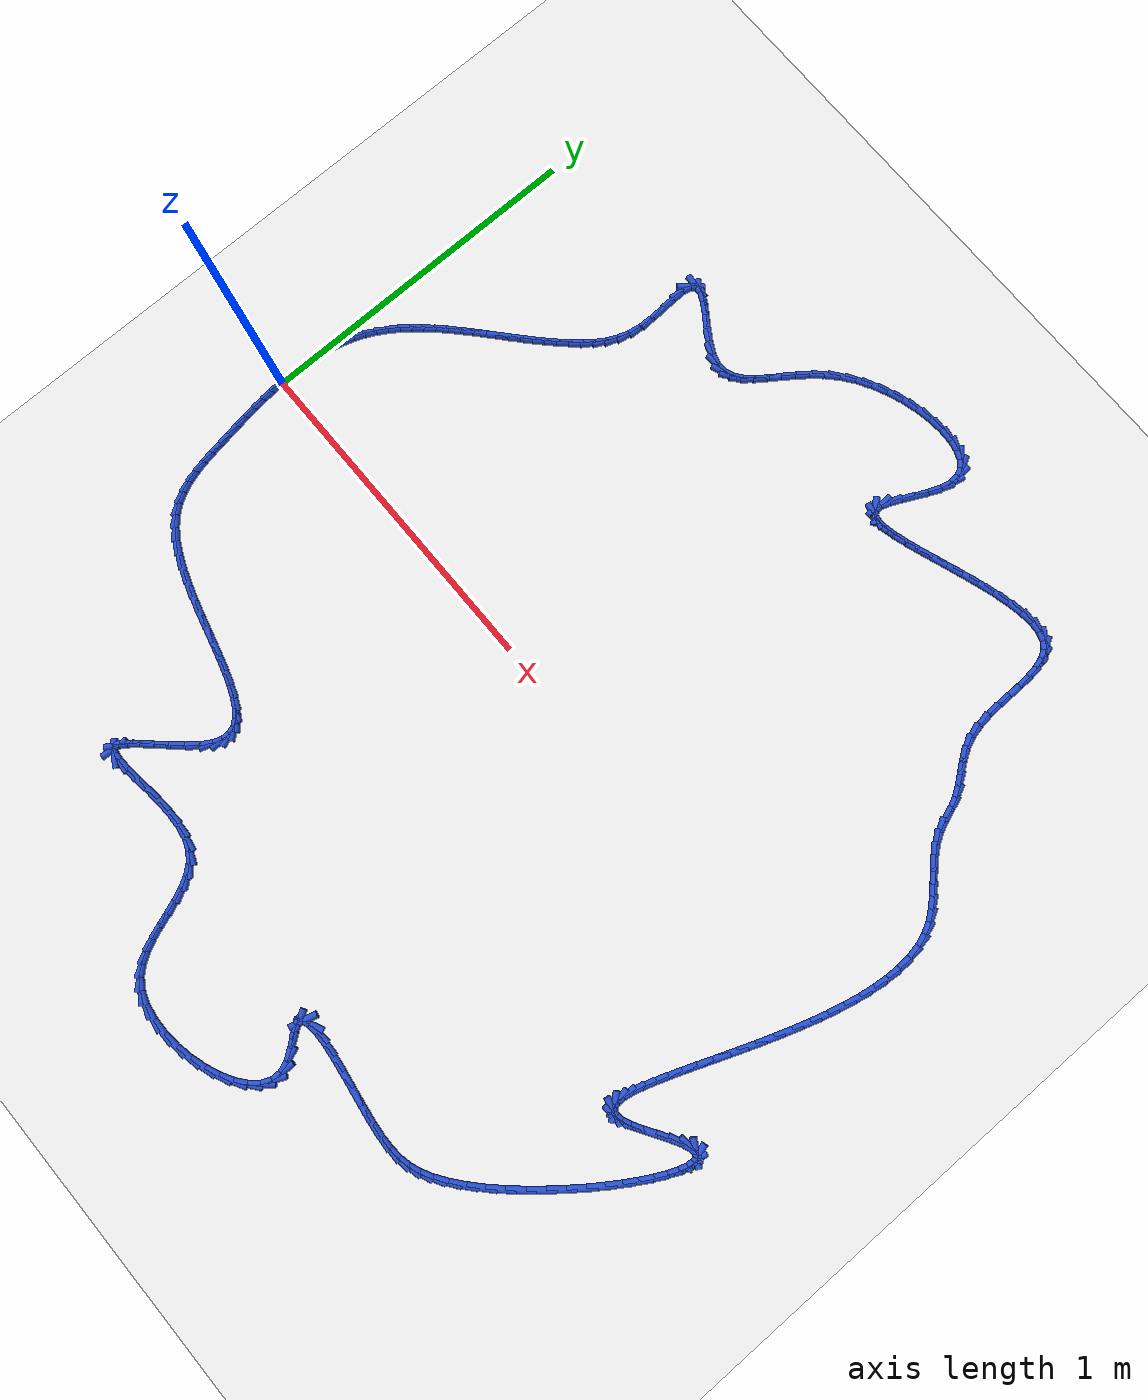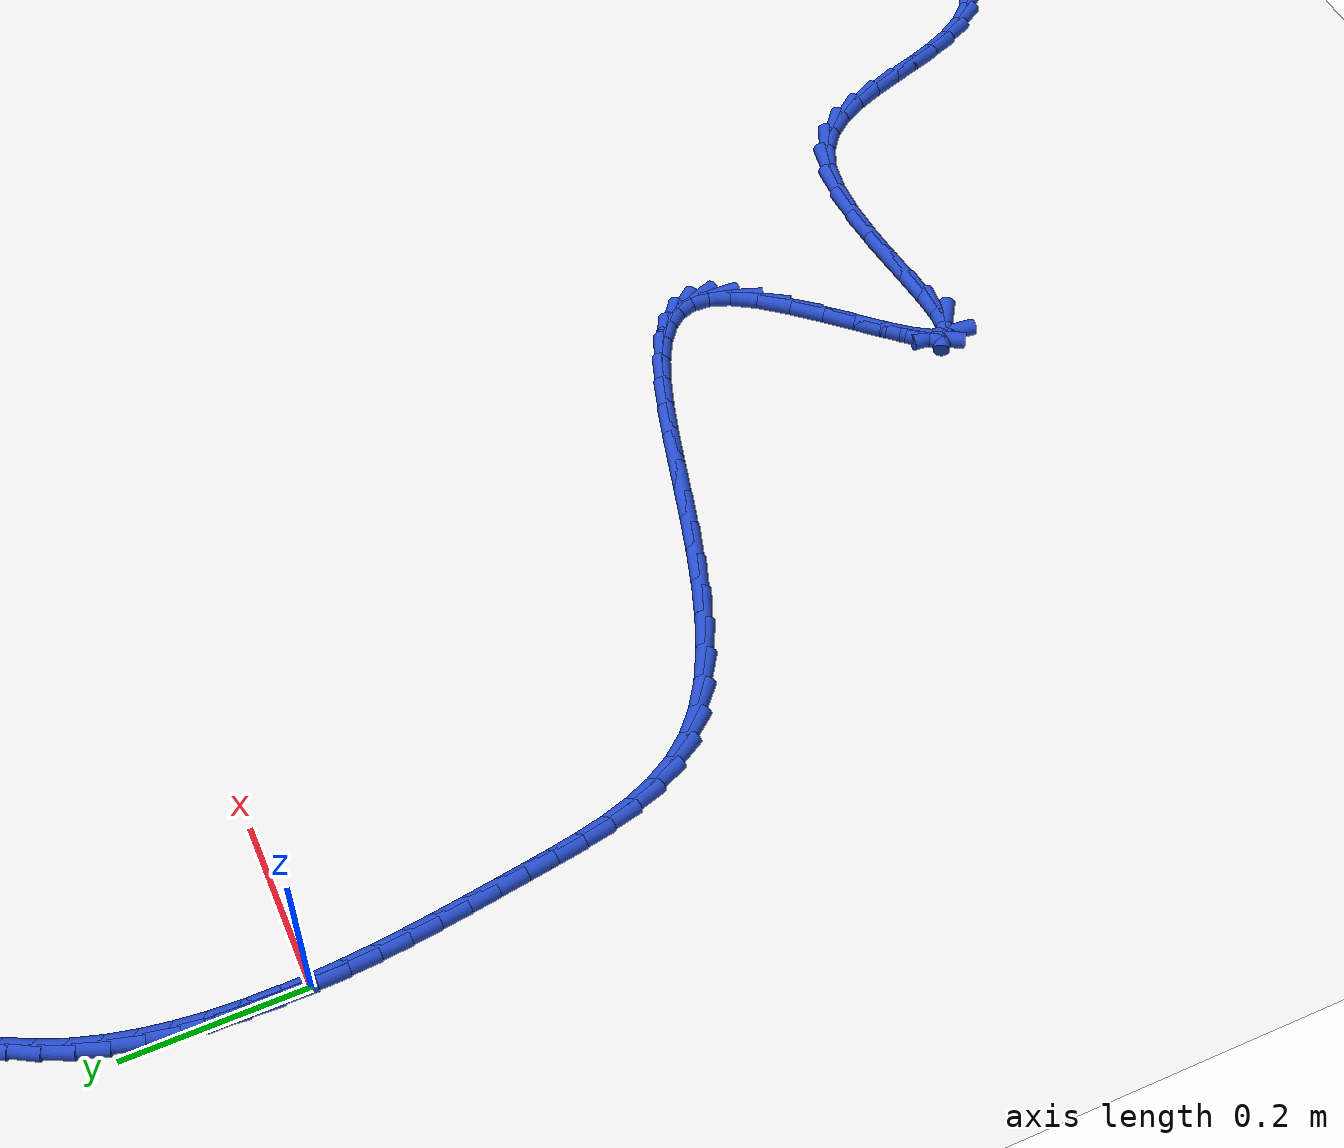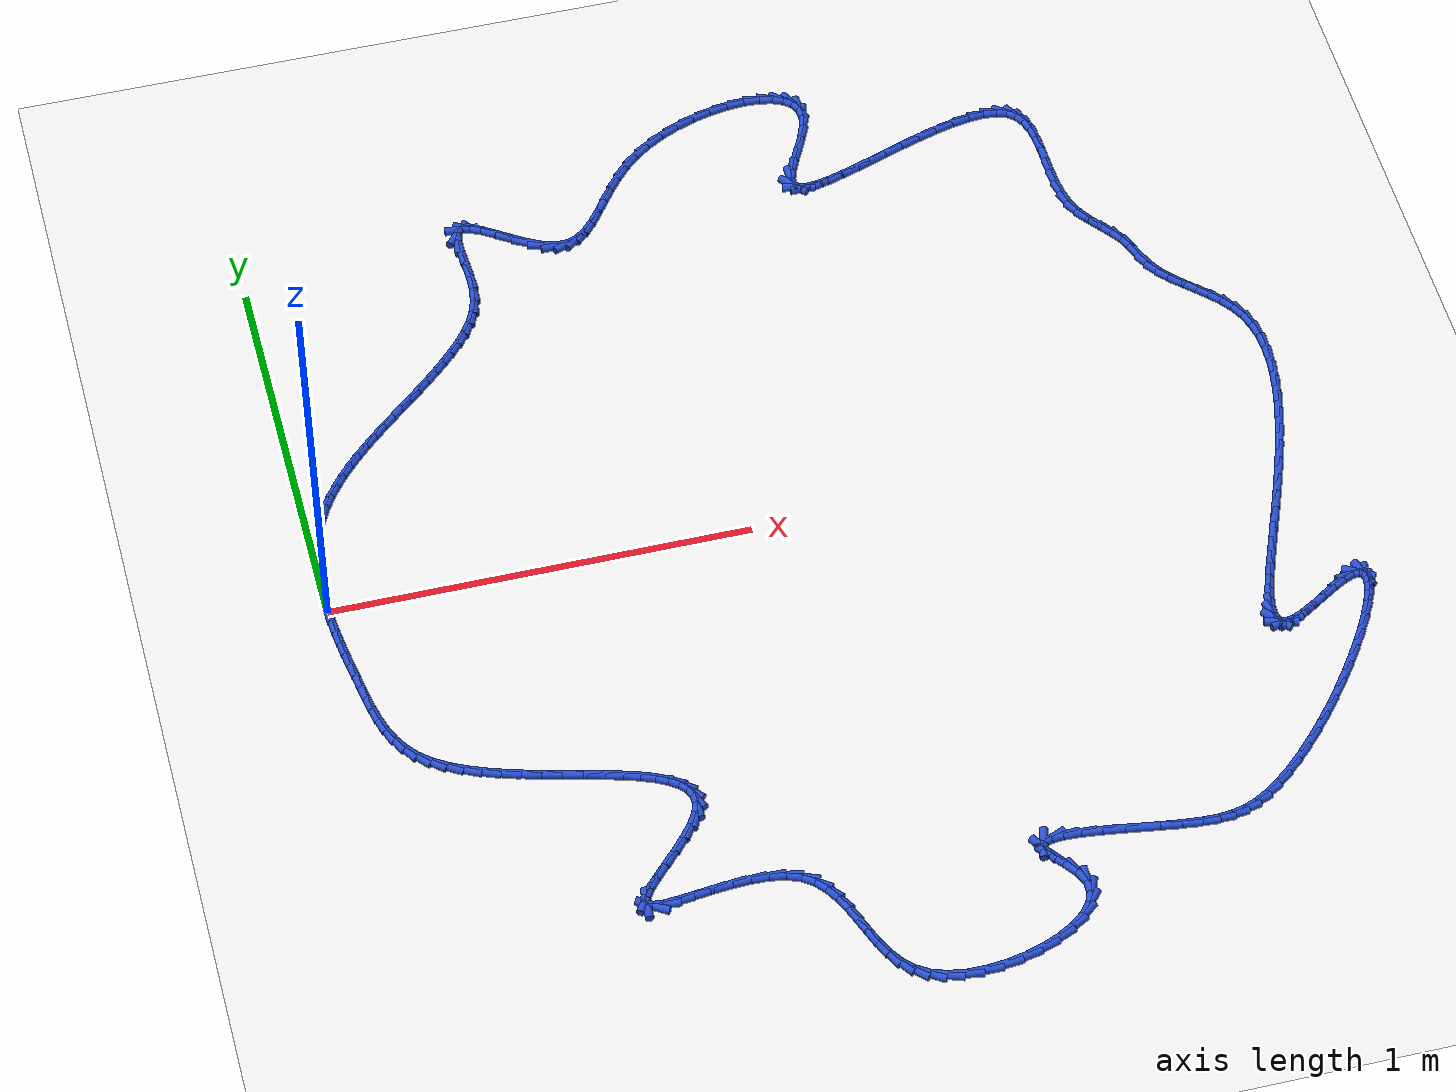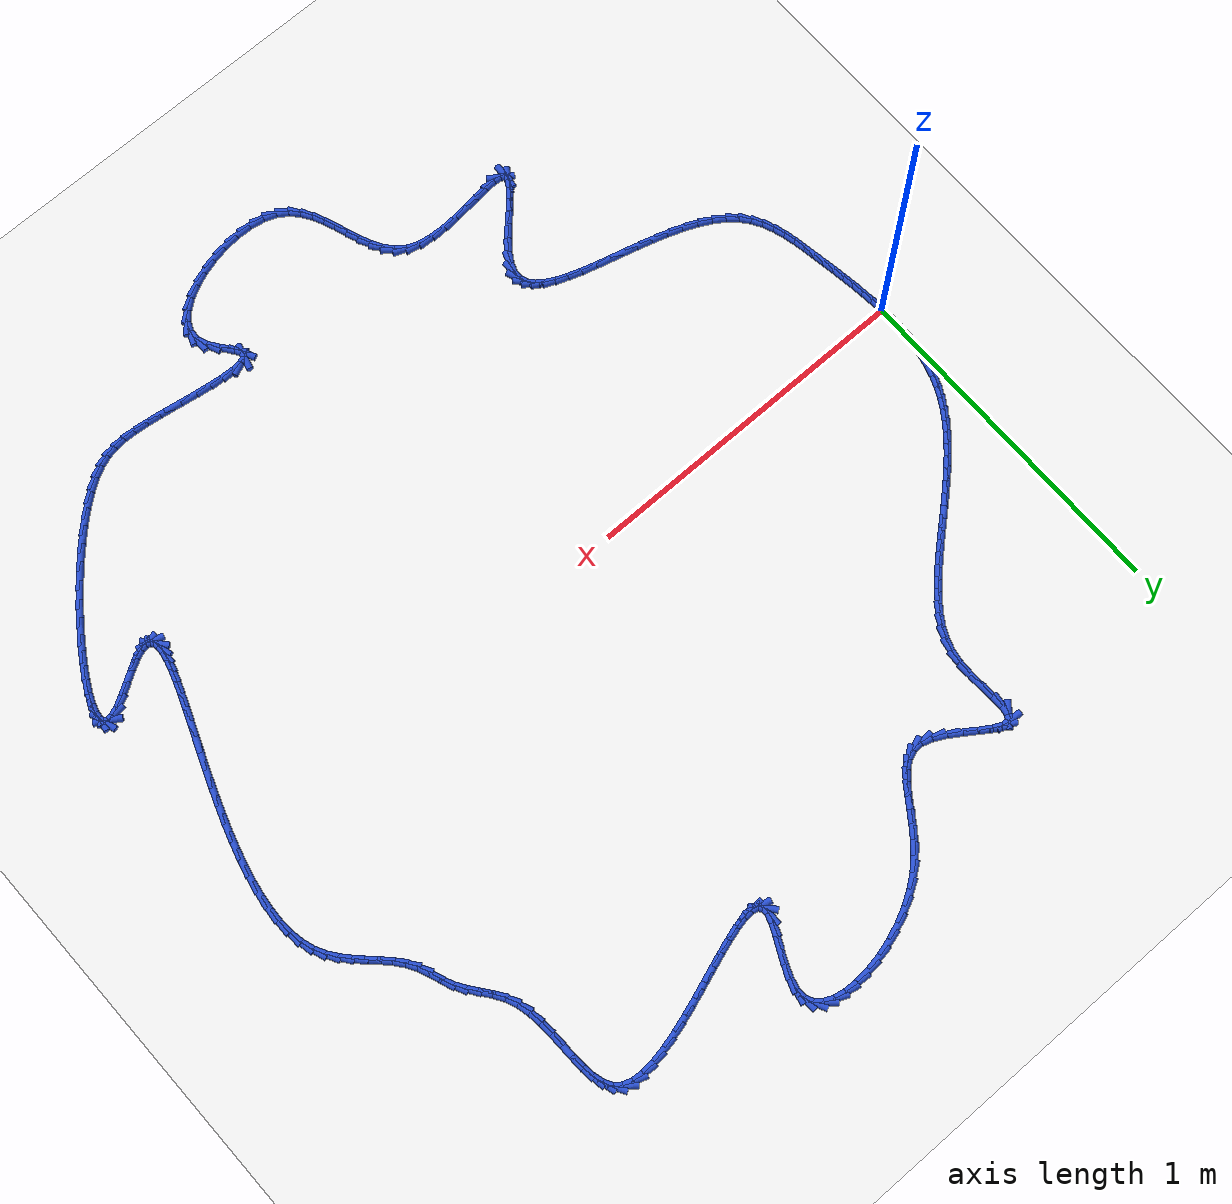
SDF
<sdf version="1.6">
 <world name="default">
  <light name="sun" type="directional">
   <pose>0 0 10 0 -0 0</pose>
   <diffuse>0.8 0.8 0.8 1</diffuse>
   <specular>0.2 0.2 0.2 1</specular>
   <attenuation>
    <range>1000</range>
    <constant>0.9</constant>
    <linear>0.01</linear>
    <quadratic>0.001</quadratic>
   </attenuation>
   <direction>-0.5 0.1 -0.9</direction>
  </light>
  <model name="ground_plane">
   <static>1</static>
   <link name="link">
    <collision name="collision">
     <geometry><plane><normal>0 0 1</normal><size>100 100</size></plane></geometry>
     <surface><friction><ode><mu>100</mu><mu2>50</mu2></ode></friction></surface>
    </collision>
    <visual name="visual">
     <cast_shadows>0</cast_shadows>
     <geometry><plane><normal>0 0 1</normal><size>100 100</size></plane></geometry>
     <material>
      <script><uri>file://media/materials/scripts/gazebo.material</uri><name>Gazebo/WhiteGlow</name></script>
     </material>
    </visual>
   </link>
  </model>
  <gravity>0 0 -9.8</gravity>
  <magnetic_field>6e-06 2.3e-05 -4.2e-05</magnetic_field>
  <atmosphere type="adiabatic"/>
  <physics name="default_physics" default="0" type="ode">
   <max_step_size>0.001</max_step_size>
   <real_time_factor>1</real_time_factor>
   <real_time_update_rate>1000</real_time_update_rate>
  </physics>
  <scene><ambient>0.4 0.4 0.4 1</ambient><background>0.7 0.7 0.7 1</background><shadows>1</shadows></scene>
  <spherical_coordinates>
   <surface_model>EARTH_WGS84</surface_model>
   <latitude_deg>0</latitude_deg>
   <longitude_deg>0</longitude_deg>
   <elevation>0</elevation>
   <heading_deg>0</heading_deg>
  </spherical_coordinates>
  <model name="line">
   <link name="link_0">
    <pose>1.214306433183765e-17 -5.551115123125783e-17 0.01 0 1.57 -1.544926847063853</pose>
    <collision name="collision">
     <geometry><cylinder><radius>0.01</radius><length>0.08</length></cylinder></geometry>
    </collision>
    <visual name="visual">
     <material>
      <script><name>Gazebo/Blue</name><uri>file://media/materials/scripts/gazebo.material</uri></script>
     </material>
     <geometry><cylinder><radius>0.01</radius><length>0.08</length></cylinder></geometry>
    </visual>
   </link>
   <link name="link_1">
    <pose>-0.0008951007464306239 0.03459292845237338 0.01 0 1.57 1.5587647873589767</pose>
    <collision name="collision">
     <geometry><cylinder><radius>0.01</radius><length>0.08</length></cylinder></geometry>
    </collision>
    <visual name="visual">
     <material>
      <script><name>Gazebo/Blue</name><uri>file://media/materials/scripts/gazebo.material</uri></script>
     </material>
     <geometry><cylinder><radius>0.01</radius><length>0.08</length></cylinder></geometry>
    </visual>
   </link>
   <link name="link_2">
    <pose>-0.00047655189180878695 0.06937888918215812 0.01 0 1.57 1.5151115104201591</pose>
    <collision name="collision">
     <geometry><cylinder><radius>0.01</radius><length>0.08</length></cylinder></geometry>
    </collision>
    <visual name="visual">
     <material>
      <script><name>Gazebo/Blue</name><uri>file://media/materials/scripts/gazebo.material</uri></script>
     </material>
     <geometry><cylinder><radius>0.01</radius><length>0.08</length></cylinder></geometry>
    </visual>
   </link>
   <link name="link_3">
    <pose>0.0014596562780407518 0.10411378853131274 0.01 0 1.57 1.464982097356111</pose>
    <collision name="collision">
     <geometry><cylinder><radius>0.01</radius><length>0.08</length></cylinder></geometry>
    </collision>
    <visual name="visual">
     <material>
      <script><name>Gazebo/Blue</name><uri>file://media/materials/scripts/gazebo.material</uri></script>
     </material>
     <geometry><cylinder><radius>0.01</radius><length>0.08</length></cylinder></geometry>
    </visual>
   </link>
   <link name="link_4">
    <pose>0.0051175334772932245 0.13855353284179592 0.01 0 1.57 1.407557626411429</pose>
    <collision name="collision">
     <geometry><cylinder><radius>0.01</radius><length>0.08</length></cylinder></geometry>
    </collision>
    <visual name="visual">
     <material>
      <script><name>Gazebo/Blue</name><uri>file://media/materials/scripts/gazebo.material</uri></script>
     </material>
     <geometry><cylinder><radius>0.01</radius><length>0.08</length></cylinder></geometry>
    </visual>
   </link>
   <link name="link_5">
    <pose>0.010701089420123865 0.1724540284555663 0.01 0 1.57 1.3419679618454743</pose>
    <collision name="collision">
     <geometry><cylinder><radius>0.01</radius><length>0.08</length></cylinder></geometry>
    </collision>
    <visual name="visual">
     <material>
      <script><name>Gazebo/Blue</name><uri>file://media/materials/scripts/gazebo.material</uri></script>
     </material>
     <geometry><cylinder><radius>0.01</radius><length>0.08</length></cylinder></geometry>
    </visual>
   </link>
   <link name="link_6">
    <pose>0.018414333820707895 0.20557118171458244 0.01 0 1.57 1.2673748061256054</pose>
    <collision name="collision">
     <geometry><cylinder><radius>0.01</radius><length>0.08</length></cylinder></geometry>
    </collision>
    <visual name="visual">
     <material>
      <script><name>Gazebo/Blue</name><uri>file://media/materials/scripts/gazebo.material</uri></script>
     </material>
     <geometry><cylinder><radius>0.01</radius><length>0.08</length></cylinder></geometry>
    </visual>
   </link>
   <link name="link_7">
    <pose>0.02846127639322056 0.23766089896080309 0.01 0 1.57 1.18531420956852</pose>
    <collision name="collision">
     <geometry><cylinder><radius>0.01</radius><length>0.08</length></cylinder></geometry>
    </collision>
    <visual name="visual">
     <material>
      <script><name>Gazebo/Blue</name><uri>file://media/materials/scripts/gazebo.material</uri></script>
     </material>
     <geometry><cylinder><radius>0.01</radius><length>0.08</length></cylinder></geometry>
    </visual>
   </link>
   <link name="link_8">
    <pose>0.04098678274133821 0.26852836624558746 0.01 0 1.57 1.106307680856895</pose>
    <collision name="collision">
     <geometry><cylinder><radius>0.01</radius><length>0.08</length></cylinder></geometry>
    </collision>
    <visual name="visual">
     <material>
      <script><name>Gazebo/Blue</name><uri>file://media/materials/scripts/gazebo.material</uri></script>
     </material>
     <geometry><cylinder><radius>0.01</radius><length>0.08</length></cylinder></geometry>
    </visual>
   </link>
   <link name="link_9">
    <pose>0.055858635920563095 0.2982096387184829 0.01 0 1.57 1.03435345917394</pose>
    <collision name="collision">
     <geometry><cylinder><radius>0.01</radius><length>0.08</length></cylinder></geometry>
    </collision>
    <visual name="visual">
     <material>
      <script><name>Gazebo/Blue</name><uri>file://media/materials/scripts/gazebo.material</uri></script>
     </material>
     <geometry><cylinder><radius>0.01</radius><length>0.08</length></cylinder></geometry>
    </visual>
   </link>
   <link name="link_10">
    <pose>0.07286354577327306 0.3268083228769097 0.01 0 1.57 0.970081321235818</pose>
    <collision name="collision">
     <geometry><cylinder><radius>0.01</radius><length>0.08</length></cylinder></geometry>
    </collision>
    <visual name="visual">
     <material>
      <script><name>Gazebo/Blue</name><uri>file://media/materials/scripts/gazebo.material</uri></script>
     </material>
     <geometry><cylinder><radius>0.01</radius><length>0.08</length></cylinder></geometry>
    </visual>
   </link>
   <link name="link_11">
    <pose>0.09178821202149028 0.3544280336507117 0.01 0 1.57 0.9137269030067781</pose>
    <collision name="collision">
     <geometry><cylinder><radius>0.01</radius><length>0.08</length></cylinder></geometry>
    </collision>
    <visual name="visual">
     <material>
      <script><name>Gazebo/Blue</name><uri>file://media/materials/scripts/gazebo.material</uri></script>
     </material>
     <geometry><cylinder><radius>0.01</radius><length>0.08</length></cylinder></geometry>
    </visual>
   </link>
   <link name="link_12">
    <pose>0.11241933438723695 0.38117238596973274 0.01 0 1.57 0.8652401237360117</pose>
    <collision name="collision">
     <geometry><cylinder><radius>0.01</radius><length>0.08</length></cylinder></geometry>
    </collision>
    <visual name="visual">
     <material>
      <script><name>Gazebo/Blue</name><uri>file://media/materials/scripts/gazebo.material</uri></script>
     </material>
     <geometry><cylinder><radius>0.01</radius><length>0.08</length></cylinder></geometry>
    </visual>
   </link>
   <link name="link_13">
    <pose>0.13454361259253514 0.40714499476381644 0.01 0 1.57 0.8243929727467321</pose>
    <collision name="collision">
     <geometry><cylinder><radius>0.01</radius><length>0.08</length></cylinder></geometry>
    </collision>
    <visual name="visual">
     <material>
      <script><name>Gazebo/Blue</name><uri>file://media/materials/scripts/gazebo.material</uri></script>
     </material>
     <geometry><cylinder><radius>0.01</radius><length>0.08</length></cylinder></geometry>
    </visual>
   </link>
   <link name="link_14">
    <pose>0.157947746359407 0.4324494749628068 0.01 0 1.57 0.7908700432687833</pose>
    <collision name="collision">
     <geometry><cylinder><radius>0.01</radius><length>0.08</length></cylinder></geometry>
    </collision>
    <visual name="visual">
     <material>
      <script><name>Gazebo/Blue</name><uri>file://media/materials/scripts/gazebo.material</uri></script>
     </material>
     <geometry><cylinder><radius>0.01</radius><length>0.08</length></cylinder></geometry>
    </visual>
   </link>
   <link name="link_15">
    <pose>0.18241843540987476 0.4571894414965475 0.01 0 1.57 0.76433650375186</pose>
    <collision name="collision">
     <geometry><cylinder><radius>0.01</radius><length>0.08</length></cylinder></geometry>
    </collision>
    <visual name="visual">
     <material>
      <script><name>Gazebo/Blue</name><uri>file://media/materials/scripts/gazebo.material</uri></script>
     </material>
     <geometry><cylinder><radius>0.01</radius><length>0.08</length></cylinder></geometry>
    </visual>
   </link>
   <link name="link_16">
    <pose>0.2077423794659606 0.4814685092948824 0.01 0 1.57 0.7444851171360718</pose>
    <collision name="collision">
     <geometry><cylinder><radius>0.01</radius><length>0.08</length></cylinder></geometry>
    </collision>
    <visual name="visual">
     <material>
      <script><name>Gazebo/Blue</name><uri>file://media/materials/scripts/gazebo.material</uri></script>
     </material>
     <geometry><cylinder><radius>0.01</radius><length>0.08</length></cylinder></geometry>
    </visual>
   </link>
   <link name="link_17">
    <pose>0.2337062782496866 0.5053902932876554 0.01 0 1.57 0.7310667381546199</pose>
    <collision name="collision">
     <geometry><cylinder><radius>0.01</radius><length>0.08</length></cylinder></geometry>
    </collision>
    <visual name="visual">
     <material>
      <script><name>Gazebo/Blue</name><uri>file://media/materials/scripts/gazebo.material</uri></script>
     </material>
     <geometry><cylinder><radius>0.01</radius><length>0.08</length></cylinder></geometry>
    </visual>
   </link>
   <link name="link_18">
    <pose>0.26009683148307483 0.52905840840471 0.01 0 1.57 0.7239090352658616</pose>
    <collision name="collision">
     <geometry><cylinder><radius>0.01</radius><length>0.08</length></cylinder></geometry>
    </collision>
    <visual name="visual">
     <material>
      <script><name>Gazebo/Blue</name><uri>file://media/materials/scripts/gazebo.material</uri></script>
     </material>
     <geometry><cylinder><radius>0.01</radius><length>0.08</length></cylinder></geometry>
    </visual>
   </link>
   <link name="link_19">
    <pose>0.2867007388881476 0.5525764695758903 0.01 0 1.57 0.722927332170416</pose>
    <collision name="collision">
     <geometry><cylinder><radius>0.01</radius><length>0.08</length></cylinder></geometry>
    </collision>
    <visual name="visual">
     <material>
      <script><name>Gazebo/Blue</name><uri>file://media/materials/scripts/gazebo.material</uri></script>
     </material>
     <geometry><cylinder><radius>0.01</radius><length>0.08</length></cylinder></geometry>
    </visual>
   </link>
   <link name="link_20">
    <pose>0.313304700186927 0.5760480917310401 0.01 0 1.57 0.728130226930549</pose>
    <collision name="collision">
     <geometry><cylinder><radius>0.01</radius><length>0.08</length></cylinder></geometry>
    </collision>
    <visual name="visual">
     <material>
      <script><name>Gazebo/Blue</name><uri>file://media/materials/scripts/gazebo.material</uri></script>
     </material>
     <geometry><cylinder><radius>0.01</radius><length>0.08</length></cylinder></geometry>
    </visual>
   </link>
   <link name="link_21">
    <pose>0.33969541510143525 0.5995768898000031 0.01 0 1.57 0.7396213593491705</pose>
    <collision name="collision">
     <geometry><cylinder><radius>0.01</radius><length>0.08</length></cylinder></geometry>
    </collision>
    <visual name="visual">
     <material>
      <script><name>Gazebo/Blue</name><uri>file://media/materials/scripts/gazebo.material</uri></script>
     </material>
     <geometry><cylinder><radius>0.01</radius><length>0.08</length></cylinder></geometry>
    </visual>
   </link>
   <link name="link_22">
    <pose>0.3656595833536944 0.623266478712623 0.01 0 1.57 0.7575974249426902</pose>
    <collision name="collision">
     <geometry><cylinder><radius>0.01</radius><length>0.08</length></cylinder></geometry>
    </collision>
    <visual name="visual">
     <material>
      <script><name>Gazebo/Blue</name><uri>file://media/materials/scripts/gazebo.material</uri></script>
     </material>
     <geometry><cylinder><radius>0.01</radius><length>0.08</length></cylinder></geometry>
    </visual>
   </link>
   <link name="link_23">
    <pose>0.39098390466572663 0.6472204733987437 0.01 0 1.57 0.7823412154644398</pose>
    <collision name="collision">
     <geometry><cylinder><radius>0.01</radius><length>0.08</length></cylinder></geometry>
    </collision>
    <visual name="visual">
     <material>
      <script><name>Gazebo/Blue</name><uri>file://media/materials/scripts/gazebo.material</uri></script>
     </material>
     <geometry><cylinder><radius>0.01</radius><length>0.08</length></cylinder></geometry>
    </visual>
   </link>
   <link name="link_24">
    <pose>0.4154550787595541 0.6715424887882091 0.01 0 1.57 0.8142070201734509</pose>
    <collision name="collision">
     <geometry><cylinder><radius>0.01</radius><length>0.08</length></cylinder></geometry>
    </collision>
    <visual name="visual">
     <material>
      <script><name>Gazebo/Blue</name><uri>file://media/materials/scripts/gazebo.material</uri></script>
     </material>
     <geometry><cylinder><radius>0.01</radius><length>0.08</length></cylinder></geometry>
    </visual>
   </link>
   <link name="link_25">
    <pose>0.4388598053571991 0.6963361398108631 0.01 0 1.57 0.8536455980159612</pose>
    <collision name="collision">
     <geometry><cylinder><radius>0.01</radius><length>0.08</length></cylinder></geometry>
    </collision>
    <visual name="visual">
     <material>
      <script><name>Gazebo/Blue</name><uri>file://media/materials/scripts/gazebo.material</uri></script>
     </material>
     <geometry><cylinder><radius>0.01</radius><length>0.08</length></cylinder></geometry>
    </visual>
   </link>
   <link name="link_26">
    <pose>0.460983694516362 0.7217064264555976 0.01 0 1.57 0.9087756777116334</pose>
    <collision name="collision">
     <geometry><cylinder><radius>0.01</radius><length>0.08</length></cylinder></geometry>
    </collision>
    <visual name="visual">
     <material>
      <script><name>Gazebo/Blue</name><uri>file://media/materials/scripts/gazebo.material</uri></script>
     </material>
     <geometry><cylinder><radius>0.01</radius><length>0.08</length></cylinder></geometry>
    </visual>
   </link>
   <link name="link_27">
    <pose>0.4814490130032026 0.7479659723798768 0.01 0 1.57 0.995281110305445</pose>
    <collision name="collision">
     <geometry><cylinder><radius>0.01</radius><length>0.08</length></cylinder></geometry>
    </collision>
    <visual name="visual">
     <material>
      <script><name>Gazebo/Blue</name><uri>file://media/materials/scripts/gazebo.material</uri></script>
     </material>
     <geometry><cylinder><radius>0.01</radius><length>0.08</length></cylinder></geometry>
    </visual>
   </link>
   <link name="link_28">
    <pose>0.499542258441653 0.7758541933086223 0.01 0 1.57 1.1121240185944894</pose>
    <collision name="collision">
     <geometry><cylinder><radius>0.01</radius><length>0.08</length></cylinder></geometry>
    </collision>
    <visual name="visual">
     <material>
      <script><name>Gazebo/Blue</name><uri>file://media/materials/scripts/gazebo.material</uri></script>
     </material>
     <geometry><cylinder><radius>0.01</radius><length>0.08</length></cylinder></geometry>
    </visual>
   </link>
   <link name="link_29">
    <pose>0.5145086319465483 0.8061629964565344 0.01 0 1.57 1.2514388526522295</pose>
    <collision name="collision">
     <geometry><cylinder><radius>0.01</radius><length>0.08</length></cylinder></geometry>
    </collision>
    <visual name="visual">
     <material>
      <script><name>Gazebo/Blue</name><uri>file://media/materials/scripts/gazebo.material</uri></script>
     </material>
     <geometry><cylinder><radius>0.01</radius><length>0.08</length></cylinder></geometry>
    </visual>
   </link>
   <link name="link_30">
    <pose>0.5255933346327225 0.8396842890383127 0.01 0 1.57 1.4006230942406581</pose>
    <collision name="collision">
     <geometry><cylinder><radius>0.01</radius><length>0.08</length></cylinder></geometry>
    </collision>
    <visual name="visual">
     <material>
      <script><name>Gazebo/Blue</name><uri>file://media/materials/scripts/gazebo.material</uri></script>
     </material>
     <geometry><cylinder><radius>0.01</radius><length>0.08</length></cylinder></geometry>
    </visual>
   </link>
   <link name="link_31">
    <pose>0.5320415676150105 0.8772099782686569 0.01 0 1.57 1.535913963452869</pose>
    <collision name="collision">
     <geometry><cylinder><radius>0.01</radius><length>0.08</length></cylinder></geometry>
    </collision>
    <visual name="visual">
     <material>
      <script><name>Gazebo/Blue</name><uri>file://media/materials/scripts/gazebo.material</uri></script>
     </material>
     <geometry><cylinder><radius>0.01</radius><length>0.08</length></cylinder></geometry>
    </visual>
   </link>
   <link name="link_32">
    <pose>0.5334997255463951 0.9189951764311219 0.01 0 1.57 -1.5315017738230157</pose>
    <collision name="collision">
     <geometry><cylinder><radius>0.01</radius><length>0.08</length></cylinder></geometry>
    </collision>
    <visual name="visual">
     <material>
      <script><name>Gazebo/Blue</name><uri>file://media/materials/scripts/gazebo.material</uri></script>
     </material>
     <geometry><cylinder><radius>0.01</radius><length>0.08</length></cylinder></geometry>
    </visual>
   </link>
   <link name="link_33">
    <pose>0.5317941284710648 0.9623782666274562 0.01 0 1.57 -1.5150600373453742</pose>
    <collision name="collision">
     <geometry><cylinder><radius>0.01</radius><length>0.08</length></cylinder></geometry>
    </collision>
    <visual name="visual">
     <material>
      <script><name>Gazebo/Blue</name><uri>file://media/materials/scripts/gazebo.material</uri></script>
     </material>
     <geometry><cylinder><radius>0.01</radius><length>0.08</length></cylinder></geometry>
    </visual>
   </link>
   <link name="link_34">
    <pose>0.5294879675997813 1.0037117020539847 0.01 0 1.57 -1.5611726398477452</pose>
    <collision name="collision">
     <geometry><cylinder><radius>0.01</radius><length>0.08</length></cylinder></geometry>
    </collision>
    <visual name="visual">
     <material>
      <script><name>Gazebo/Blue</name><uri>file://media/materials/scripts/gazebo.material</uri></script>
     </material>
     <geometry><cylinder><radius>0.01</radius><length>0.08</length></cylinder></geometry>
    </visual>
   </link>
   <link name="link_35">
    <pose>0.52914501250069 1.039347162067769 0.01 0 1.57 1.4129662551251418</pose>
    <collision name="collision">
     <geometry><cylinder><radius>0.01</radius><length>0.08</length></cylinder></geometry>
    </collision>
    <visual name="visual">
     <material>
      <script><name>Gazebo/Blue</name><uri>file://media/materials/scripts/gazebo.material</uri></script>
     </material>
     <geometry><cylinder><radius>0.01</radius><length>0.08</length></cylinder></geometry>
    </visual>
   </link>
   <link name="link_36">
    <pose>0.5333290327419363 1.0656363260258717 0.01 0 1.57 0.8676204023357369</pose>
    <collision name="collision">
     <geometry><cylinder><radius>0.01</radius><length>0.08</length></cylinder></geometry>
    </collision>
    <visual name="visual">
     <material>
      <script><name>Gazebo/Blue</name><uri>file://media/materials/scripts/gazebo.material</uri></script>
     </material>
     <geometry><cylinder><radius>0.01</radius><length>0.08</length></cylinder></geometry>
    </visual>
   </link>
   <link name="link_37">
    <pose>0.5446019231055773 1.0789340307001445 0.01 0 1.57 -0.07382589816377619</pose>
    <collision name="collision">
     <geometry><cylinder><radius>0.01</radius><length>0.08</length></cylinder></geometry>
    </collision>
    <visual name="visual">
     <material>
      <script><name>Gazebo/Blue</name><uri>file://media/materials/scripts/gazebo.material</uri></script>
     </material>
     <geometry><cylinder><radius>0.01</radius><length>0.08</length></cylinder></geometry>
    </visual>
   </link>
   <link name="link_38">
    <pose>0.5644130377800939 1.0774687944234675 0.01 0 1.57 -0.4504795299516295</pose>
    <collision name="collision">
     <geometry><cylinder><radius>0.01</radius><length>0.08</length></cylinder></geometry>
    </collision>
    <visual name="visual">
     <material>
      <script><name>Gazebo/Blue</name><uri>file://media/materials/scripts/gazebo.material</uri></script>
     </material>
     <geometry><cylinder><radius>0.01</radius><length>0.08</length></cylinder></geometry>
    </visual>
   </link>
   <link name="link_39">
    <pose>0.5912232917615687 1.0645021055105586 0.01 0 1.57 -0.5700971323501393</pose>
    <collision name="collision">
     <geometry><cylinder><radius>0.01</radius><length>0.08</length></cylinder></geometry>
    </collision>
    <visual name="visual">
     <material>
      <script><name>Gazebo/Blue</name><uri>file://media/materials/scripts/gazebo.material</uri></script>
     </material>
     <geometry><cylinder><radius>0.01</radius><length>0.08</length></cylinder></geometry>
    </visual>
   </link>
   <link name="link_40">
    <pose>0.6229969964794991 1.0441318055303217 0.01 0 1.57 -0.5987331556341006</pose>
    <collision name="collision">
     <geometry><cylinder><radius>0.01</radius><length>0.08</length></cylinder></geometry>
    </collision>
    <visual name="visual">
     <material>
      <script><name>Gazebo/Blue</name><uri>file://media/materials/scripts/gazebo.material</uri></script>
     </material>
     <geometry><cylinder><radius>0.01</radius><length>0.08</length></cylinder></geometry>
    </visual>
   </link>
   <link name="link_41">
    <pose>0.6576984633633826 1.0204557360516617 0.01 0 1.57 -0.571385898219003</pose>
    <collision name="collision">
     <geometry><cylinder><radius>0.01</radius><length>0.08</length></cylinder></geometry>
    </collision>
    <visual name="visual">
     <material>
      <script><name>Gazebo/Blue</name><uri>file://media/materials/scripts/gazebo.material</uri></script>
     </material>
     <geometry><cylinder><radius>0.01</radius><length>0.08</length></cylinder></geometry>
    </visual>
   </link>
   <link name="link_42">
    <pose>0.6932920038427162 0.997571738643482 0.01 0 1.57 -0.4813482849226254</pose>
    <collision name="collision">
     <geometry><cylinder><radius>0.01</radius><length>0.08</length></cylinder></geometry>
    </collision>
    <visual name="visual">
     <material>
      <script><name>Gazebo/Blue</name><uri>file://media/materials/scripts/gazebo.material</uri></script>
     </material>
     <geometry><cylinder><radius>0.01</radius><length>0.08</length></cylinder></geometry>
    </visual>
   </link>
   <link name="link_43">
    <pose>0.7277419293469974 0.9795776548746884 0.01 0 1.57 -0.283592251510044</pose>
    <collision name="collision">
     <geometry><cylinder><radius>0.01</radius><length>0.08</length></cylinder></geometry>
    </collision>
    <visual name="visual">
     <material>
      <script><name>Gazebo/Blue</name><uri>file://media/materials/scripts/gazebo.material</uri></script>
     </material>
     <geometry><cylinder><radius>0.01</radius><length>0.08</length></cylinder></geometry>
    </visual>
   </link>
   <link name="link_44">
    <pose>0.7590798604285746 0.9704442885070499 0.01 0 1.57 0.03650759873008971</pose>
    <collision name="collision">
     <geometry><cylinder><radius>0.01</radius><length>0.08</length></cylinder></geometry>
    </collision>
    <visual name="visual">
     <material>
      <script><name>Gazebo/Blue</name><uri>file://media/materials/scripts/gazebo.material</uri></script>
     </material>
     <geometry><cylinder><radius>0.01</radius><length>0.08</length></cylinder></geometry>
    </visual>
   </link>
   <link name="link_45">
    <pose>0.7867611531163278 0.9714553152398221 0.01 0 1.57 0.37846014052318083</pose>
    <collision name="collision">
     <geometry><cylinder><radius>0.01</radius><length>0.08</length></cylinder></geometry>
    </collision>
    <visual name="visual">
     <material>
      <script><name>Gazebo/Blue</name><uri>file://media/materials/scripts/gazebo.material</uri></script>
     </material>
     <geometry><cylinder><radius>0.01</radius><length>0.08</length></cylinder></geometry>
    </visual>
   </link>
   <link name="link_46">
    <pose>0.8115990493494645 0.9813315657807004 0.01 0 1.57 0.6494577219285567</pose>
    <collision name="collision">
     <geometry><cylinder><radius>0.01</radius><length>0.08</length></cylinder></geometry>
    </collision>
    <visual name="visual">
     <material>
      <script><name>Gazebo/Blue</name><uri>file://media/materials/scripts/gazebo.material</uri></script>
     </material>
     <geometry><cylinder><radius>0.01</radius><length>0.08</length></cylinder></geometry>
    </visual>
   </link>
   <link name="link_47">
    <pose>0.8344609210179161 0.9986917071194603 0.01 0 1.57 0.8231872077643589</pose>
    <collision name="collision">
     <geometry><cylinder><radius>0.01</radius><length>0.08</length></cylinder></geometry>
    </collision>
    <visual name="visual">
     <material>
      <script><name>Gazebo/Blue</name><uri>file://media/materials/scripts/gazebo.material</uri></script>
     </material>
     <geometry><cylinder><radius>0.01</radius><length>0.08</length></cylinder></geometry>
    </visual>
   </link>
   <link name="link_48">
    <pose>0.8562141400116151 1.0221544062458776 0.01 0 1.57 0.9188564925058843</pose>
    <collision name="collision">
     <geometry><cylinder><radius>0.01</radius><length>0.08</length></cylinder></geometry>
    </collision>
    <visual name="visual">
     <material>
      <script><name>Gazebo/Blue</name><uri>file://media/materials/scripts/gazebo.material</uri></script>
     </material>
     <geometry><cylinder><radius>0.01</radius><length>0.08</length></cylinder></geometry>
    </visual>
   </link>
   <link name="link_49">
    <pose>0.8777260782204938 1.0503383301497289 0.01 0 1.57 0.9585527607999449</pose>
    <collision name="collision">
     <geometry><cylinder><radius>0.01</radius><length>0.08</length></cylinder></geometry>
    </collision>
    <visual name="visual">
     <material>
      <script><name>Gazebo/Blue</name><uri>file://media/materials/scripts/gazebo.material</uri></script>
     </material>
     <geometry><cylinder><radius>0.01</radius><length>0.08</length></cylinder></geometry>
    </visual>
   </link>
   <link name="link_50">
    <pose>0.8998641075344842 1.0818621458207893 0.01 0 1.57 0.9561956699435422</pose>
    <collision name="collision">
     <geometry><cylinder><radius>0.01</radius><length>0.08</length></cylinder></geometry>
    </collision>
    <visual name="visual">
     <material>
      <script><name>Gazebo/Blue</name><uri>file://media/materials/scripts/gazebo.material</uri></script>
     </material>
     <geometry><cylinder><radius>0.01</radius><length>0.08</length></cylinder></geometry>
    </visual>
   </link>
   <link name="link_51">
    <pose>0.923495599843518 1.1153445202488348 0.01 0 1.57 0.9189369640931082</pose>
    <collision name="collision">
     <geometry><cylinder><radius>0.01</radius><length>0.08</length></cylinder></geometry>
    </collision>
    <visual name="visual">
     <material>
      <script><name>Gazebo/Blue</name><uri>file://media/materials/scripts/gazebo.material</uri></script>
     </material>
     <geometry><cylinder><radius>0.01</radius><length>0.08</length></cylinder></geometry>
    </visual>
   </link>
   <link name="link_52">
    <pose>0.9494879270375282 1.1494041204236414 0.01 0 1.57 0.8498927072878796</pose>
    <collision name="collision">
     <geometry><cylinder><radius>0.01</radius><length>0.08</length></cylinder></geometry>
    </collision>
    <visual name="visual">
     <material>
      <script><name>Gazebo/Blue</name><uri>file://media/materials/scripts/gazebo.material</uri></script>
     </material>
     <geometry><cylinder><radius>0.01</radius><length>0.08</length></cylinder></geometry>
    </visual>
   </link>
   <link name="link_53">
    <pose>0.9787084610064462 1.182659613334985 0.01 0 1.57 0.7505294227934914</pose>
    <collision name="collision">
     <geometry><cylinder><radius>0.01</radius><length>0.08</length></cylinder></geometry>
    </collision>
    <visual name="visual">
     <material>
      <script><name>Gazebo/Blue</name><uri>file://media/materials/scripts/gazebo.material</uri></script>
     </material>
     <geometry><cylinder><radius>0.01</radius><length>0.08</length></cylinder></geometry>
    </visual>
   </link>
   <link name="link_54">
    <pose>1.0120245191701374 1.2137296974897323 0.01 0 1.57 0.6321547613784081</pose>
    <collision name="collision">
     <geometry><cylinder><radius>0.01</radius><length>0.08</length></cylinder></geometry>
    </collision>
    <visual name="visual">
     <material>
      <script><name>Gazebo/Blue</name><uri>file://media/materials/scripts/gazebo.material</uri></script>
     </material>
     <geometry><cylinder><radius>0.01</radius><length>0.08</length></cylinder></geometry>
    </visual>
   </link>
   <link name="link_55">
    <pose>1.0498969725883187 1.2414682465570874 0.01 0 1.57 0.5253664358243341</pose>
    <collision name="collision">
     <geometry><cylinder><radius>0.01</radius><length>0.08</length></cylinder></geometry>
    </collision>
    <visual name="visual">
     <material>
      <script><name>Gazebo/Blue</name><uri>file://media/materials/scripts/gazebo.material</uri></script>
     </material>
     <geometry><cylinder><radius>0.01</radius><length>0.08</length></cylinder></geometry>
    </visual>
   </link>
   <link name="link_56">
    <pose>1.0914030597294173 1.26552972206034 0.01 0 1.57 0.4312248397256465</pose>
    <collision name="collision">
     <geometry><cylinder><radius>0.01</radius><length>0.08</length></cylinder></geometry>
    </collision>
    <visual name="visual">
     <material>
      <script><name>Gazebo/Blue</name><uri>file://media/materials/scripts/gazebo.material</uri></script>
     </material>
     <geometry><cylinder><radius>0.01</radius><length>0.08</length></cylinder></geometry>
    </visual>
   </link>
   <link name="link_57">
    <pose>1.135325857598065 1.2857387911803637 0.01 0 1.57 0.34432293093883287</pose>
    <collision name="collision">
     <geometry><cylinder><radius>0.01</radius><length>0.08</length></cylinder></geometry>
    </collision>
    <visual name="visual">
     <material>
      <script><name>Gazebo/Blue</name><uri>file://media/materials/scripts/gazebo.material</uri></script>
     </material>
     <geometry><cylinder><radius>0.01</radius><length>0.08</length></cylinder></geometry>
    </visual>
   </link>
   <link name="link_58">
    <pose>1.1804484431988933 1.3019201210980322 0.01 0 1.57 0.2595700411274996</pose>
    <collision name="collision">
     <geometry><cylinder><radius>0.01</radius><length>0.08</length></cylinder></geometry>
    </collision>
    <visual name="visual">
     <material>
      <script><name>Gazebo/Blue</name><uri>file://media/materials/scripts/gazebo.material</uri></script>
     </material>
     <geometry><cylinder><radius>0.01</radius><length>0.08</length></cylinder></geometry>
    </visual>
   </link>
   <link name="link_59">
    <pose>1.2255538935365347 1.3138983789942185 0.01 0 1.57 0.1715280085992618</pose>
    <collision name="collision">
     <geometry><cylinder><radius>0.01</radius><length>0.08</length></cylinder></geometry>
    </collision>
    <visual name="visual">
     <material>
      <script><name>Gazebo/Blue</name><uri>file://media/materials/scripts/gazebo.material</uri></script>
     </material>
     <geometry><cylinder><radius>0.01</radius><length>0.08</length></cylinder></geometry>
    </visual>
   </link>
   <link name="link_60">
    <pose>1.2694252856156198 1.321498232049797 0.01 0 1.57 0.07340925914924105</pose>
    <collision name="collision">
     <geometry><cylinder><radius>0.01</radius><length>0.08</length></cylinder></geometry>
    </collision>
    <visual name="visual">
     <material>
      <script><name>Gazebo/Blue</name><uri>file://media/materials/scripts/gazebo.material</uri></script>
     </material>
     <geometry><cylinder><radius>0.01</radius><length>0.08</length></cylinder></geometry>
    </visual>
   </link>
   <link name="link_61">
    <pose>1.3108456964407815 1.3245443474456406 0.01 0 1.57 -0.04454913707649983</pose>
    <collision name="collision">
     <geometry><cylinder><radius>0.01</radius><length>0.08</length></cylinder></geometry>
    </collision>
    <visual name="visual">
     <material>
      <script><name>Gazebo/Blue</name><uri>file://media/materials/scripts/gazebo.material</uri></script>
     </material>
     <geometry><cylinder><radius>0.01</radius><length>0.08</length></cylinder></geometry>
    </visual>
   </link>
   <link name="link_62">
    <pose>1.3485982030166508 1.322861392362623 0.01 0 1.57 -0.19779990248411605</pose>
    <collision name="collision">
     <geometry><cylinder><radius>0.01</radius><length>0.08</length></cylinder></geometry>
    </collision>
    <visual name="visual">
     <material>
      <script><name>Gazebo/Blue</name><uri>file://media/materials/scripts/gazebo.material</uri></script>
     </material>
     <geometry><cylinder><radius>0.01</radius><length>0.08</length></cylinder></geometry>
    </visual>
   </link>
   <link name="link_63">
    <pose>1.38146588234786 1.3162740339816177 0.01 0 1.57 -0.4110612394811182</pose>
    <collision name="collision">
     <geometry><cylinder><radius>0.01</radius><length>0.08</length></cylinder></geometry>
    </collision>
    <visual name="visual">
     <material>
      <script><name>Gazebo/Blue</name><uri>file://media/materials/scripts/gazebo.material</uri></script>
     </material>
     <geometry><cylinder><radius>0.01</radius><length>0.08</length></cylinder></geometry>
    </visual>
   </link>
   <link name="link_64">
    <pose>1.4082318114390402 1.3046069394834985 0.01 0 1.57 -0.7160803997855721</pose>
    <collision name="collision">
     <geometry><cylinder><radius>0.01</radius><length>0.08</length></cylinder></geometry>
    </collision>
    <visual name="visual">
     <material>
      <script><name>Gazebo/Blue</name><uri>file://media/materials/scripts/gazebo.material</uri></script>
     </material>
     <geometry><cylinder><radius>0.01</radius><length>0.08</length></cylinder></geometry>
    </visual>
   </link>
   <link name="link_65">
    <pose>1.4276790672948225 1.2876847760491377 0.01 0 1.57 -1.1166643688333866</pose>
    <collision name="collision">
     <geometry><cylinder><radius>0.01</radius><length>0.08</length></cylinder></geometry>
    </collision>
    <visual name="visual">
     <material>
      <script><name>Gazebo/Blue</name><uri>file://media/materials/scripts/gazebo.material</uri></script>
     </material>
     <geometry><cylinder><radius>0.01</radius><length>0.08</length></cylinder></geometry>
    </visual>
   </link>
   <link name="link_66">
    <pose>1.4385907269198408 1.2653322108594105 0.01 0 1.57 -1.52751569397766</pose>
    <collision name="collision">
     <geometry><cylinder><radius>0.01</radius><length>0.08</length></cylinder></geometry>
    </collision>
    <visual name="visual">
     <material>
      <script><name>Gazebo/Blue</name><uri>file://media/materials/scripts/gazebo.material</uri></script>
     </material>
     <geometry><cylinder><radius>0.01</radius><length>0.08</length></cylinder></geometry>
    </visual>
   </link>
   <link name="link_67">
    <pose>1.4398003749811532 1.2374007186718072 0.01 0 1.57 1.3351703215894337</pose>
    <collision name="collision">
     <geometry><cylinder><radius>0.01</radius><length>0.08</length></cylinder></geometry>
    </collision>
    <visual name="visual">
     <material>
      <script><name>Gazebo/Blue</name><uri>file://media/materials/scripts/gazebo.material</uri></script>
     </material>
     <geometry><cylinder><radius>0.01</radius><length>0.08</length></cylinder></geometry>
    </visual>
   </link>
   <link name="link_68">
    <pose>1.431949754938029 1.2047014772478541 0.01 0 1.57 1.1945654742467418</pose>
    <collision name="collision">
     <geometry><cylinder><radius>0.01</radius><length>0.08</length></cylinder></geometry>
    </collision>
    <visual name="visual">
     <material>
      <script><name>Gazebo/Blue</name><uri>file://media/materials/scripts/gazebo.material</uri></script>
     </material>
     <geometry><cylinder><radius>0.01</radius><length>0.08</length></cylinder></geometry>
    </visual>
   </link>
   <link name="link_69">
    <pose>1.4179433674102047 1.1692466511504918 0.01 0 1.57 1.1283277954971953</pose>
    <collision name="collision">
     <geometry><cylinder><radius>0.01</radius><length>0.08</length></cylinder></geometry>
    </collision>
    <visual name="visual">
     <material>
      <script><name>Gazebo/Blue</name><uri>file://media/materials/scripts/gazebo.material</uri></script>
     </material>
     <geometry><cylinder><radius>0.01</radius><length>0.08</length></cylinder></geometry>
    </visual>
   </link>
   <link name="link_70">
    <pose>1.4008285763501114 1.133124231452003 0.01 0 1.57 1.1111953745332535</pose>
    <collision name="collision">
     <geometry><cylinder><radius>0.01</radius><length>0.08</length></cylinder></geometry>
    </collision>
    <visual name="visual">
     <material>
      <script><name>Gazebo/Blue</name><uri>file://media/materials/scripts/gazebo.material</uri></script>
     </material>
     <geometry><cylinder><radius>0.01</radius><length>0.08</length></cylinder></geometry>
    </visual>
   </link>
   <link name="link_71">
    <pose>1.3836527457101795 1.0984222092246725 0.01 0 1.57 1.1438877256201196</pose>
    <collision name="collision">
     <geometry><cylinder><radius>0.01</radius><length>0.08</length></cylinder></geometry>
    </collision>
    <visual name="visual">
     <material>
      <script><name>Gazebo/Blue</name><uri>file://media/materials/scripts/gazebo.material</uri></script>
     </material>
     <geometry><cylinder><radius>0.01</radius><length>0.08</length></cylinder></geometry>
    </visual>
   </link>
   <link name="link_72">
    <pose>1.3694632394428397 1.0672285755407835 0.01 0 1.57 1.2623449579647152</pose>
    <collision name="collision">
     <geometry><cylinder><radius>0.01</radius><length>0.08</length></cylinder></geometry>
    </collision>
    <visual name="visual">
     <material>
      <script><name>Gazebo/Blue</name><uri>file://media/materials/scripts/gazebo.material</uri></script>
     </material>
     <geometry><cylinder><radius>0.01</radius><length>0.08</length></cylinder></geometry>
    </visual>
   </link>
   <link name="link_73">
    <pose>1.3613074215005216 1.04163132147262 0.01 0 1.57 -1.535478849969414</pose>
    <collision name="collision">
     <geometry><cylinder><radius>0.01</radius><length>0.08</length></cylinder></geometry>
    </collision>
    <visual name="visual">
     <material>
      <script><name>Gazebo/Blue</name><uri>file://media/materials/scripts/gazebo.material</uri></script>
     </material>
     <geometry><cylinder><radius>0.01</radius><length>0.08</length></cylinder></geometry>
    </visual>
   </link>
   <link name="link_74">
    <pose>1.3619478165530037 1.0235063355506058 0.01 0 1.57 -0.8294352258811661</pose>
    <collision name="collision">
     <geometry><cylinder><radius>0.01</radius><length>0.08</length></cylinder></geometry>
    </collision>
    <visual name="visual">
     <material>
      <script><name>Gazebo/Blue</name><uri>file://media/materials/scripts/gazebo.material</uri></script>
     </material>
     <geometry><cylinder><radius>0.01</radius><length>0.08</length></cylinder></geometry>
    </visual>
   </link>
   <link name="link_75">
    <pose>1.3716715003988025 1.0128861896356736 0.01 0 1.57 -0.22243288934570224</pose>
    <collision name="collision">
     <geometry><cylinder><radius>0.01</radius><length>0.08</length></cylinder></geometry>
    </collision>
    <visual name="visual">
     <material>
      <script><name>Gazebo/Blue</name><uri>file://media/materials/scripts/gazebo.material</uri></script>
     </material>
     <geometry><cylinder><radius>0.01</radius><length>0.08</length></cylinder></geometry>
    </visual>
   </link>
   <link name="link_76">
    <pose>1.389492525996471 1.0088555126727112 0.01 0 1.57 0.06553578116865108</pose>
    <collision name="collision">
     <geometry><cylinder><radius>0.01</radius><length>0.08</length></cylinder></geometry>
    </collision>
    <visual name="visual">
     <material>
      <script><name>Gazebo/Blue</name><uri>file://media/materials/scripts/gazebo.material</uri></script>
     </material>
     <geometry><cylinder><radius>0.01</radius><length>0.08</length></cylinder></geometry>
    </visual>
   </link>
   <link name="link_77">
    <pose>1.4144144722168281 1.0104911341885925 0.01 0 1.57 0.202765433576069</pose>
    <collision name="collision">
     <geometry><cylinder><radius>0.01</radius><length>0.08</length></cylinder></geometry>
    </collision>
    <visual name="visual">
     <material>
      <script><name>Gazebo/Blue</name><uri>file://media/materials/scripts/gazebo.material</uri></script>
     </material>
     <geometry><cylinder><radius>0.01</radius><length>0.08</length></cylinder></geometry>
    </visual>
   </link>
   <link name="link_78">
    <pose>1.445440917930695 1.0168698837101922 0.01 0 1.57 0.27508718112653463</pose>
    <collision name="collision">
     <geometry><cylinder><radius>0.01</radius><length>0.08</length></cylinder></geometry>
    </collision>
    <visual name="visual">
     <material>
      <script><name>Gazebo/Blue</name><uri>file://media/materials/scripts/gazebo.material</uri></script>
     </material>
     <geometry><cylinder><radius>0.01</radius><length>0.08</length></cylinder></geometry>
    </visual>
   </link>
   <link name="link_79">
    <pose>1.4815754420088896 1.0270685907643837 0.01 0 1.57 0.3145798634617396</pose>
    <collision name="collision">
     <geometry><cylinder><radius>0.01</radius><length>0.08</length></cylinder></geometry>
    </collision>
    <visual name="visual">
     <material>
      <script><name>Gazebo/Blue</name><uri>file://media/materials/scripts/gazebo.material</uri></script>
     </material>
     <geometry><cylinder><radius>0.01</radius><length>0.08</length></cylinder></geometry>
    </visual>
   </link>
   <link name="link_80">
    <pose>1.5218216233222324 1.0401640848780418 0.01 0 1.57 0.33446686454200925</pose>
    <collision name="collision">
     <geometry><cylinder><radius>0.01</radius><length>0.08</length></cylinder></geometry>
    </collision>
    <visual name="visual">
     <material>
      <script><name>Gazebo/Blue</name><uri>file://media/materials/scripts/gazebo.material</uri></script>
     </material>
     <geometry><cylinder><radius>0.01</radius><length>0.08</length></cylinder></geometry>
    </visual>
   </link>
   <link name="link_81">
    <pose>1.5651830407415421 1.0552331955780403 0.01 0 1.57 0.3406158648645442</pose>
    <collision name="collision">
     <geometry><cylinder><radius>0.01</radius><length>0.08</length></cylinder></geometry>
    </collision>
    <visual name="visual">
     <material>
      <script><name>Gazebo/Blue</name><uri>file://media/materials/scripts/gazebo.material</uri></script>
     </material>
     <geometry><cylinder><radius>0.01</radius><length>0.08</length></cylinder></geometry>
    </visual>
   </link>
   <link name="link_82">
    <pose>1.6106632731376398 1.0713527523912543 0.01 0 1.57 0.33544919490871633</pose>
    <collision name="collision">
     <geometry><cylinder><radius>0.01</radius><length>0.08</length></cylinder></geometry>
    </collision>
    <visual name="visual">
     <material>
      <script><name>Gazebo/Blue</name><uri>file://media/materials/scripts/gazebo.material</uri></script>
     </material>
     <geometry><cylinder><radius>0.01</radius><length>0.08</length></cylinder></geometry>
    </visual>
   </link>
   <link name="link_83">
    <pose>1.6572658993813447 1.087599584844557 0.01 0 1.57 0.3193360513407432</pose>
    <collision name="collision">
     <geometry><cylinder><radius>0.01</radius><length>0.08</length></cylinder></geometry>
    </collision>
    <visual name="visual">
     <material>
      <script><name>Gazebo/Blue</name><uri>file://media/materials/scripts/gazebo.material</uri></script>
     </material>
     <geometry><cylinder><radius>0.01</radius><length>0.08</length></cylinder></geometry>
    </visual>
   </link>
   <link name="link_84">
    <pose>1.7039944983434754 1.103050522464823 0.01 0 1.57 0.29094510941008966</pose>
    <collision name="collision">
     <geometry><cylinder><radius>0.01</radius><length>0.08</length></cylinder></geometry>
    </collision>
    <visual name="visual">
     <material>
      <script><name>Gazebo/Blue</name><uri>file://media/materials/scripts/gazebo.material</uri></script>
     </material>
     <geometry><cylinder><radius>0.01</radius><length>0.08</length></cylinder></geometry>
    </visual>
   </link>
   <link name="link_85">
    <pose>1.7498526488948518 1.1167823947789264 0.01 0 1.57 0.24694207028499693</pose>
    <collision name="collision">
     <geometry><cylinder><radius>0.01</radius><length>0.08</length></cylinder></geometry>
    </collision>
    <visual name="visual">
     <material>
      <script><name>Gazebo/Blue</name><uri>file://media/materials/scripts/gazebo.material</uri></script>
     </material>
     <geometry><cylinder><radius>0.01</radius><length>0.08</length></cylinder></geometry>
    </visual>
   </link>
   <link name="link_86">
    <pose>1.7938439299062958 1.127872031313742 0.01 0 1.57 0.1809456920667266</pose>
    <collision name="collision">
     <geometry><cylinder><radius>0.01</radius><length>0.08</length></cylinder></geometry>
    </collision>
    <visual name="visual">
     <material>
      <script><name>Gazebo/Blue</name><uri>file://media/materials/scripts/gazebo.material</uri></script>
     </material>
     <geometry><cylinder><radius>0.01</radius><length>0.08</length></cylinder></geometry>
    </visual>
   </link>
   <link name="link_87">
    <pose>1.8349719202486237 1.1353962615961433 0.01 0 1.57 0.08127465651905086</pose>
    <collision name="collision">
     <geometry><cylinder><radius>0.01</radius><length>0.08</length></cylinder></geometry>
    </collision>
    <visual name="visual">
     <material>
      <script><name>Gazebo/Blue</name><uri>file://media/materials/scripts/gazebo.material</uri></script>
     </material>
     <geometry><cylinder><radius>0.01</radius><length>0.08</length></cylinder></geometry>
    </visual>
   </link>
   <link name="link_88">
    <pose>1.8722401987926565 1.138431915153005 0.01 0 1.57 -0.07317783989855912</pose>
    <collision name="collision">
     <geometry><cylinder><radius>0.01</radius><length>0.08</length></cylinder></geometry>
    </collision>
    <visual name="visual">
     <material>
      <script><name>Gazebo/Blue</name><uri>file://media/materials/scripts/gazebo.material</uri></script>
     </material>
     <geometry><cylinder><radius>0.01</radius><length>0.08</length></cylinder></geometry>
    </visual>
   </link>
   <link name="link_89">
    <pose>1.904652344409214 1.136055821511201 0.01 0 1.57 -0.31692472183013215</pose>
    <collision name="collision">
     <geometry><cylinder><radius>0.01</radius><length>0.08</length></cylinder></geometry>
    </collision>
    <visual name="visual">
     <material>
      <script><name>Gazebo/Blue</name><uri>file://media/materials/scripts/gazebo.material</uri></script>
     </material>
     <geometry><cylinder><radius>0.01</radius><length>0.08</length></cylinder></geometry>
    </visual>
   </link>
   <link name="link_90">
    <pose>1.9312119359691162 1.127344810197606 0.01 0 1.57 -0.6757893627709982</pose>
    <collision name="collision">
     <geometry><cylinder><radius>0.01</radius><length>0.08</length></cylinder></geometry>
    </collision>
    <visual name="visual">
     <material>
      <script><name>Gazebo/Blue</name><uri>file://media/materials/scripts/gazebo.material</uri></script>
     </material>
     <geometry><cylinder><radius>0.01</radius><length>0.08</length></cylinder></geometry>
    </visual>
   </link>
   <link name="link_91">
    <pose>1.9510199143903584 1.111464340828231 0.01 0 1.57 -1.0370361517819378</pose>
    <collision name="collision">
     <geometry><cylinder><radius>0.01</radius><length>0.08</length></cylinder></geometry>
    </collision>
    <visual name="visual">
     <material>
      <script><name>Gazebo/Blue</name><uri>file://media/materials/scripts/gazebo.material</uri></script>
     </material>
     <geometry><cylinder><radius>0.01</radius><length>0.08</length></cylinder></geometry>
    </visual>
   </link>
   <link name="link_92">
    <pose>1.9644502683308276 1.0887387469123089 0.01 0 1.57 -1.2861083012736771</pose>
    <collision name="collision">
     <geometry><cylinder><radius>0.01</radius><length>0.08</length></cylinder></geometry>
    </collision>
    <visual name="visual">
     <material>
      <script><name>Gazebo/Blue</name><uri>file://media/materials/scripts/gazebo.material</uri></script>
     </material>
     <geometry><cylinder><radius>0.01</radius><length>0.08</length></cylinder></geometry>
    </visual>
   </link>
   <link name="link_93">
    <pose>1.9727707484949444 1.060305966563222 0.01 0 1.57 -1.4353014730007148</pose>
    <collision name="collision">
     <geometry><cylinder><radius>0.01</radius><length>0.08</length></cylinder></geometry>
    </collision>
    <visual name="visual">
     <material>
      <script><name>Gazebo/Blue</name><uri>file://media/materials/scripts/gazebo.material</uri></script>
     </material>
     <geometry><cylinder><radius>0.01</radius><length>0.08</length></cylinder></geometry>
    </visual>
   </link>
   <link name="link_94">
    <pose>1.977267622506675 1.0273207941158207 0.01 0 1.57 -1.5169894276503961</pose>
    <collision name="collision">
     <geometry><cylinder><radius>0.01</radius><length>0.08</length></cylinder></geometry>
    </collision>
    <visual name="visual">
     <material>
      <script><name>Gazebo/Blue</name><uri>file://media/materials/scripts/gazebo.material</uri></script>
     </material>
     <geometry><cylinder><radius>0.01</radius><length>0.08</length></cylinder></geometry>
    </visual>
   </link>
   <link name="link_95">
    <pose>1.979227157989987 0.990938023904959 0.01 0 1.57 -1.5524565306420446</pose>
    <collision name="collision">
     <geometry><cylinder><radius>0.01</radius><length>0.08</length></cylinder></geometry>
    </collision>
    <visual name="visual">
     <material>
      <script><name>Gazebo/Blue</name><uri>file://media/materials/scripts/gazebo.material</uri></script>
     </material>
     <geometry><cylinder><radius>0.01</radius><length>0.08</length></cylinder></geometry>
    </visual>
   </link>
   <link name="link_96">
    <pose>1.9799356225688467 0.9523124502654885 0.01 0 1.57 -1.5520728990859043</pose>
    <collision name="collision">
     <geometry><cylinder><radius>0.01</radius><length>0.08</length></cylinder></geometry>
    </collision>
    <visual name="visual">
     <material>
      <script><name>Gazebo/Blue</name><uri>file://media/materials/scripts/gazebo.material</uri></script>
     </material>
     <geometry><cylinder><radius>0.01</radius><length>0.08</length></cylinder></geometry>
    </visual>
   </link>
   <link name="link_97">
    <pose>1.980679283867222 0.9125988675322616 0.01 0 1.57 -1.5187552760902108</pose>
    <collision name="collision">
     <geometry><cylinder><radius>0.01</radius><length>0.08</length></cylinder></geometry>
    </collision>
    <visual name="visual">
     <material>
      <script><name>Gazebo/Blue</name><uri>file://media/materials/scripts/gazebo.material</uri></script>
     </material>
     <geometry><cylinder><radius>0.01</radius><length>0.08</length></cylinder></geometry>
    </visual>
   </link>
   <link name="link_98">
    <pose>1.982744409509079 0.87295207004013 0.01 0 1.57 -1.4497814091476202</pose>
    <collision name="collision">
     <geometry><cylinder><radius>0.01</radius><length>0.08</length></cylinder></geometry>
    </collision>
    <visual name="visual">
     <material>
      <script><name>Gazebo/Blue</name><uri>file://media/materials/scripts/gazebo.material</uri></script>
     </material>
     <geometry><cylinder><radius>0.01</radius><length>0.08</length></cylinder></geometry>
    </visual>
   </link>
   <link name="link_99">
    <pose>1.9874172671183854 0.8345268521239458 0.01 0 1.57 -1.3374784938455375</pose>
    <collision name="collision">
     <geometry><cylinder><radius>0.01</radius><length>0.08</length></cylinder></geometry>
    </collision>
    <visual name="visual">
     <material>
      <script><name>Gazebo/Blue</name><uri>file://media/materials/scripts/gazebo.material</uri></script>
     </material>
     <geometry><cylinder><radius>0.01</radius><length>0.08</length></cylinder></geometry>
    </visual>
   </link>
   <link name="link_100">
    <pose>1.9959841243191079 0.7984780081185623 0.01 0 1.57 -1.1741037704281179</pose>
    <collision name="collision">
     <geometry><cylinder><radius>0.01</radius><length>0.08</length></cylinder></geometry>
    </collision>
    <visual name="visual">
     <material>
      <script><name>Gazebo/Blue</name><uri>file://media/materials/scripts/gazebo.material</uri></script>
     </material>
     <geometry><cylinder><radius>0.01</radius><length>0.08</length></cylinder></geometry>
    </visual>
   </link>
   <link name="link_101">
    <pose>2.0096356249442655 0.7658890821615515 0.01 0 1.57 -1.0172007712883406</pose>
    <collision name="collision">
     <geometry><cylinder><radius>0.01</radius><length>0.08</length></cylinder></geometry>
    </collision>
    <visual name="visual">
     <material>
      <script><name>Gazebo/Blue</name><uri>file://media/materials/scripts/gazebo.material</uri></script>
     </material>
     <geometry><cylinder><radius>0.01</radius><length>0.08</length></cylinder></geometry>
    </visual>
   </link>
   <link name="link_102">
    <pose>2.0277870808167755 0.7365208016029207 0.01 0 1.57 -0.9311847909002186</pose>
    <collision name="collision">
     <geometry><cylinder><radius>0.01</radius><length>0.08</length></cylinder></geometry>
    </collision>
    <visual name="visual">
     <material>
      <script><name>Gazebo/Blue</name><uri>file://media/materials/scripts/gazebo.material</uri></script>
     </material>
     <geometry><cylinder><radius>0.01</radius><length>0.08</length></cylinder></geometry>
    </visual>
   </link>
   <link name="link_103">
    <pose>2.0482862716049106 0.7089659106563336 0.01 0 1.57 -0.9214556130622783</pose>
    <collision name="collision">
     <geometry><cylinder><radius>0.01</radius><length>0.08</length></cylinder></geometry>
    </collision>
    <visual name="visual">
     <material>
      <script><name>Gazebo/Blue</name><uri>file://media/materials/scripts/gazebo.material</uri></script>
     </material>
     <geometry><cylinder><radius>0.01</radius><length>0.08</length></cylinder></geometry>
    </visual>
   </link>
   <link name="link_104">
    <pose>2.068927115152473 0.6817770205771035 0.01 0 1.57 -0.9894457167972587</pose>
    <collision name="collision">
     <geometry><cylinder><radius>0.01</radius><length>0.08</length></cylinder></geometry>
    </collision>
    <visual name="visual">
     <material>
      <script><name>Gazebo/Blue</name><uri>file://media/materials/scripts/gazebo.material</uri></script>
     </material>
     <geometry><cylinder><radius>0.01</radius><length>0.08</length></cylinder></geometry>
    </visual>
   </link>
   <link name="link_105">
    <pose>2.0875035293032678 0.653506742620545 0.01 0 1.57 -1.1295151932228582</pose>
    <collision name="collision">
     <geometry><cylinder><radius>0.01</radius><length>0.08</length></cylinder></geometry>
    </collision>
    <visual name="visual">
     <material>
      <script><name>Gazebo/Blue</name><uri>file://media/materials/scripts/gazebo.material</uri></script>
     </material>
     <geometry><cylinder><radius>0.01</radius><length>0.08</length></cylinder></geometry>
    </visual>
   </link>
   <link name="link_106">
    <pose>2.1019957489271084 0.6228254141699873 0.01 0 1.57 -1.2237822130924656</pose>
    <collision name="collision">
     <geometry><cylinder><radius>0.01</radius><length>0.08</length></cylinder></geometry>
    </collision>
    <visual name="visual">
     <material>
      <script><name>Gazebo/Blue</name><uri>file://media/materials/scripts/gazebo.material</uri></script>
     </material>
     <geometry><cylinder><radius>0.01</radius><length>0.08</length></cylinder></geometry>
    </visual>
   </link>
   <link name="link_107">
    <pose>2.1136891624885688 0.5904917643330045 0.01 0 1.57 -1.178182355609783</pose>
    <collision name="collision">
     <geometry><cylinder><radius>0.01</radius><length>0.08</length></cylinder></geometry>
    </collision>
    <visual name="visual">
     <material>
      <script><name>Gazebo/Blue</name><uri>file://media/materials/scripts/gazebo.material</uri></script>
     </material>
     <geometry><cylinder><radius>0.01</radius><length>0.08</length></cylinder></geometry>
    </visual>
   </link>
   <link name="link_108">
    <pose>2.126706579448025 0.5590573728631456 0.01 0 1.57 -1.0252266744634895</pose>
    <collision name="collision">
     <geometry><cylinder><radius>0.01</radius><length>0.08</length></cylinder></geometry>
    </collision>
    <visual name="visual">
     <material>
      <script><name>Gazebo/Blue</name><uri>file://media/materials/scripts/gazebo.material</uri></script>
     </material>
     <geometry><cylinder><radius>0.01</radius><length>0.08</length></cylinder></geometry>
    </visual>
   </link>
   <link name="link_109">
    <pose>2.1441028451180753 0.5303991831846511 0.01 0 1.57 -0.8928742638511952</pose>
    <collision name="collision">
     <geometry><cylinder><radius>0.01</radius><length>0.08</length></cylinder></geometry>
    </collision>
    <visual name="visual">
     <material>
      <script><name>Gazebo/Blue</name><uri>file://media/materials/scripts/gazebo.material</uri></script>
     </material>
     <geometry><cylinder><radius>0.01</radius><length>0.08</length></cylinder></geometry>
    </visual>
   </link>
   <link name="link_110">
    <pose>2.1652869809702864 0.5040910150664649 0.01 0 1.57 -0.8094926854252864</pose>
    <collision name="collision">
     <geometry><cylinder><radius>0.01</radius><length>0.08</length></cylinder></geometry>
    </collision>
    <visual name="visual">
     <material>
      <script><name>Gazebo/Blue</name><uri>file://media/materials/scripts/gazebo.material</uri></script>
     </material>
     <geometry><cylinder><radius>0.01</radius><length>0.08</length></cylinder></geometry>
    </visual>
   </link>
   <link name="link_111">
    <pose>2.1889536889969627 0.4792554415465158 0.01 0 1.57 -0.773102076718726</pose>
    <collision name="collision">
     <geometry><cylinder><radius>0.01</radius><length>0.08</length></cylinder></geometry>
    </collision>
    <visual name="visual">
     <material>
      <script><name>Gazebo/Blue</name><uri>file://media/materials/scripts/gazebo.material</uri></script>
     </material>
     <geometry><cylinder><radius>0.01</radius><length>0.08</length></cylinder></geometry>
    </visual>
   </link>
   <link name="link_112">
    <pose>2.2137976711904117 0.4550150356627312 0.01 0 1.57 -0.7814725429000222</pose>
    <collision name="collision">
     <geometry><cylinder><radius>0.01</radius><length>0.08</length></cylinder></geometry>
    </collision>
    <visual name="visual">
     <material>
      <script><name>Gazebo/Blue</name><uri>file://media/materials/scripts/gazebo.material</uri></script>
     </material>
     <geometry><cylinder><radius>0.01</radius><length>0.08</length></cylinder></geometry>
    </visual>
   </link>
   <link name="link_113">
    <pose>2.2385136295429398 0.4304923704530395 0.01 0 1.57 -0.8343677760602719</pose>
    <collision name="collision">
     <geometry><cylinder><radius>0.01</radius><length>0.08</length></cylinder></geometry>
    </collision>
    <visual name="visual">
     <material>
      <script><name>Gazebo/Blue</name><uri>file://media/materials/scripts/gazebo.material</uri></script>
     </material>
     <geometry><cylinder><radius>0.01</radius><length>0.08</length></cylinder></geometry>
    </visual>
   </link>
   <link name="link_114">
    <pose>2.2617962660468516 0.40481001895536833 0.01 0 1.57 -0.9329894824157687</pose>
    <collision name="collision">
     <geometry><cylinder><radius>0.01</radius><length>0.08</length></cylinder></geometry>
    </collision>
    <visual name="visual">
     <material>
      <script><name>Gazebo/Blue</name><uri>file://media/materials/scripts/gazebo.material</uri></script>
     </material>
     <geometry><cylinder><radius>0.01</radius><length>0.08</length></cylinder></geometry>
    </visual>
   </link>
   <link name="link_115">
    <pose>2.282340282694453 0.37709055420764526 0.01 0 1.57 -1.0767232830797087</pose>
    <collision name="collision">
     <geometry><cylinder><radius>0.01</radius><length>0.08</length></cylinder></geometry>
    </collision>
    <visual name="visual">
     <material>
      <script><name>Gazebo/Blue</name><uri>file://media/materials/scripts/gazebo.material</uri></script>
     </material>
     <geometry><cylinder><radius>0.01</radius><length>0.08</length></cylinder></geometry>
    </visual>
   </link>
   <link name="link_116">
    <pose>2.2988406233726195 0.346456728218105 0.01 0 1.57 -1.2452394849076576</pose>
    <collision name="collision">
     <geometry><cylinder><radius>0.01</radius><length>0.08</length></cylinder></geometry>
    </collision>
    <visual name="visual">
     <material>
      <script><name>Gazebo/Blue</name><uri>file://media/materials/scripts/gazebo.material</uri></script>
     </material>
     <geometry><cylinder><radius>0.01</radius><length>0.08</length></cylinder></geometry>
    </visual>
   </link>
   <link name="link_117">
    <pose>2.310367756832476 0.31230913221983514 0.01 0 1.57 -1.3921171820196896</pose>
    <collision name="collision">
     <geometry><cylinder><radius>0.01</radius><length>0.08</length></cylinder></geometry>
    </collision>
    <visual name="visual">
     <material>
      <script><name>Gazebo/Blue</name><uri>file://media/materials/scripts/gazebo.material</uri></script>
     </material>
     <geometry><cylinder><radius>0.01</radius><length>0.08</length></cylinder></geometry>
    </visual>
   </link>
   <link name="link_118">
    <pose>2.317126303926747 0.27488748148477077 0.01 0 1.57 -1.5111163441229656</pose>
    <collision name="collision">
     <geometry><cylinder><radius>0.01</radius><length>0.08</length></cylinder></geometry>
    </collision>
    <visual name="visual">
     <material>
      <script><name>Gazebo/Blue</name><uri>file://media/materials/scripts/gazebo.material</uri></script>
     </material>
     <geometry><cylinder><radius>0.01</radius><length>0.08</length></cylinder></geometry>
    </visual>
   </link>
   <link name="link_119">
    <pose>2.319534158919023 0.23458928568089898 0.01 0 1.57 1.5351629460759149</pose>
    <collision name="collision">
     <geometry><cylinder><radius>0.01</radius><length>0.08</length></cylinder></geometry>
    </collision>
    <visual name="visual">
     <material>
      <script><name>Gazebo/Blue</name><uri>file://media/materials/scripts/gazebo.material</uri></script>
     </material>
     <geometry><cylinder><radius>0.01</radius><length>0.08</length></cylinder></geometry>
    </visual>
   </link>
   <link name="link_120">
    <pose>2.3180092160728916 0.19181205447620497 0.01 0 1.57 1.4589162608870774</pose>
    <collision name="collision">
     <geometry><cylinder><radius>0.01</radius><length>0.08</length></cylinder></geometry>
    </collision>
    <visual name="visual">
     <material>
      <script><name>Gazebo/Blue</name><uri>file://media/materials/scripts/gazebo.material</uri></script>
     </material>
     <geometry><cylinder><radius>0.01</radius><length>0.08</length></cylinder></geometry>
    </visual>
   </link>
   <link name="link_121">
    <pose>2.31296936965194 0.14695329753867484 0.01 0 1.57 1.3977201433234263</pose>
    <collision name="collision">
     <geometry><cylinder><radius>0.01</radius><length>0.08</length></cylinder></geometry>
    </collision>
    <visual name="visual">
     <material>
      <script><name>Gazebo/Blue</name><uri>file://media/materials/scripts/gazebo.material</uri></script>
     </material>
     <geometry><cylinder><radius>0.01</radius><length>0.08</length></cylinder></geometry>
    </visual>
   </link>
   <link name="link_122">
    <pose>2.3048325139197576 0.10041052453629452 0.01 0 1.57 1.3483999149790504</pose>
    <collision name="collision">
     <geometry><cylinder><radius>0.01</radius><length>0.08</length></cylinder></geometry>
    </collision>
    <visual name="visual">
     <material>
      <script><name>Gazebo/Blue</name><uri>file://media/materials/scripts/gazebo.material</uri></script>
     </material>
     <geometry><cylinder><radius>0.01</radius><length>0.08</length></cylinder></geometry>
    </visual>
   </link>
   <link name="link_123">
    <pose>2.294016543139933 0.05258124513704909 0.01 0 1.57 1.308553281446863</pose>
    <collision name="collision">
     <geometry><cylinder><radius>0.01</radius><length>0.08</length></cylinder></geometry>
    </collision>
    <visual name="visual">
     <material>
      <script><name>Gazebo/Blue</name><uri>file://media/materials/scripts/gazebo.material</uri></script>
     </material>
     <geometry><cylinder><radius>0.01</radius><length>0.08</length></cylinder></geometry>
    </visual>
   </link>
   <link name="link_124">
    <pose>2.2809393515760537 0.00386296900892592 0.01 0 1.57 1.2764041503940442</pose>
    <collision name="collision">
     <geometry><cylinder><radius>0.01</radius><length>0.08</length></cylinder></geometry>
    </collision>
    <visual name="visual">
     <material>
      <script><name>Gazebo/Blue</name><uri>file://media/materials/scripts/gazebo.material</uri></script>
     </material>
     <geometry><cylinder><radius>0.01</radius><length>0.08</length></cylinder></geometry>
    </visual>
   </link>
   <link name="link_125">
    <pose>2.266018833491709 -0.04534679418008973 0.01 0 1.57 1.2506645103969396</pose>
    <collision name="collision">
     <geometry><cylinder><radius>0.01</radius><length>0.08</length></cylinder></geometry>
    </collision>
    <visual name="visual">
     <material>
      <script><name>Gazebo/Blue</name><uri>file://media/materials/scripts/gazebo.material</uri></script>
     </material>
     <geometry><cylinder><radius>0.01</radius><length>0.08</length></cylinder></geometry>
    </visual>
   </link>
   <link name="link_126">
    <pose>2.249672883150485 -0.09465053476201278 0.01 0 1.57 1.2304280265725156</pose>
    <collision name="collision">
     <geometry><cylinder><radius>0.01</radius><length>0.08</length></cylinder></geometry>
    </collision>
    <visual name="visual">
     <material>
      <script><name>Gazebo/Blue</name><uri>file://media/materials/scripts/gazebo.material</uri></script>
     </material>
     <geometry><cylinder><radius>0.01</radius><length>0.08</length></cylinder></geometry>
    </visual>
   </link>
   <link name="link_127">
    <pose>2.2323193948159723 -0.14365074306885559 0.01 0 1.57 1.2150978248597553</pose>
    <collision name="collision">
     <geometry><cylinder><radius>0.01</radius><length>0.08</length></cylinder></geometry>
    </collision>
    <visual name="visual">
     <material>
      <script><name>Gazebo/Blue</name><uri>file://media/materials/scripts/gazebo.material</uri></script>
     </material>
     <geometry><cylinder><radius>0.01</radius><length>0.08</length></cylinder></geometry>
    </visual>
   </link>
   <link name="link_128">
    <pose>2.214376262751759 -0.19194990943263332 0.01 0 1.57 1.204346188685098</pose>
    <collision name="collision">
     <geometry><cylinder><radius>0.01</radius><length>0.08</length></cylinder></geometry>
    </collision>
    <visual name="visual">
     <material>
      <script><name>Gazebo/Blue</name><uri>file://media/materials/scripts/gazebo.material</uri></script>
     </material>
     <geometry><cylinder><radius>0.01</radius><length>0.08</length></cylinder></geometry>
    </visual>
   </link>
   <link name="link_129">
    <pose>2.1962613812214324 -0.23915052418535984 0.01 0 1.57 1.1981056590028647</pose>
    <collision name="collision">
     <geometry><cylinder><radius>0.01</radius><length>0.08</length></cylinder></geometry>
    </collision>
    <visual name="visual">
     <material>
      <script><name>Gazebo/Blue</name><uri>file://media/materials/scripts/gazebo.material</uri></script>
     </material>
     <geometry><cylinder><radius>0.01</radius><length>0.08</length></cylinder></geometry>
    </visual>
   </link>
   <link name="link_130">
    <pose>2.178392644488582 -0.28485507765904927 0.01 0 1.57 1.1965963820005372</pose>
    <collision name="collision">
     <geometry><cylinder><radius>0.01</radius><length>0.08</length></cylinder></geometry>
    </collision>
    <visual name="visual">
     <material>
      <script><name>Gazebo/Blue</name><uri>file://media/materials/scripts/gazebo.material</uri></script>
     </material>
     <geometry><cylinder><radius>0.01</radius><length>0.08</length></cylinder></geometry>
    </visual>
   </link>
   <link name="link_131">
    <pose>2.1611879468167947 -0.3286660601857156 0.01 0 1.57 1.2004043943137548</pose>
    <collision name="collision">
     <geometry><cylinder><radius>0.01</radius><length>0.08</length></cylinder></geometry>
    </collision>
    <visual name="visual">
     <material>
      <script><name>Gazebo/Blue</name><uri>file://media/materials/scripts/gazebo.material</uri></script>
     </material>
     <geometry><cylinder><radius>0.01</radius><length>0.08</length></cylinder></geometry>
    </visual>
   </link>
   <link name="link_132">
    <pose>2.14506518246966 -0.3701859620973732 0.01 0 1.57 1.2106447475881221</pose>
    <collision name="collision">
     <geometry><cylinder><radius>0.01</radius><length>0.08</length></cylinder></geometry>
    </collision>
    <visual name="visual">
     <material>
      <script><name>Gazebo/Blue</name><uri>file://media/materials/scripts/gazebo.material</uri></script>
     </material>
     <geometry><cylinder><radius>0.01</radius><length>0.08</length></cylinder></geometry>
    </visual>
   </link>
   <link name="link_133">
    <pose>2.1304422457107646 -0.40901727372603675 0.01 0 1.57 1.2292849945272655</pose>
    <collision name="collision">
     <geometry><cylinder><radius>0.01</radius><length>0.08</length></cylinder></geometry>
    </collision>
    <visual name="visual">
     <material>
      <script><name>Gazebo/Blue</name><uri>file://media/materials/scripts/gazebo.material</uri></script>
     </material>
     <geometry><cylinder><radius>0.01</radius><length>0.08</length></cylinder></geometry>
    </visual>
   </link>
   <link name="link_134">
    <pose>2.1177370308036996 -0.44476248540371877 0.01 0 1.57 1.259803717543585</pose>
    <collision name="collision">
     <geometry><cylinder><radius>0.01</radius><length>0.08</length></cylinder></geometry>
    </collision>
    <visual name="visual">
     <material>
      <script><name>Gazebo/Blue</name><uri>file://media/materials/scripts/gazebo.material</uri></script>
     </material>
     <geometry><cylinder><radius>0.01</radius><length>0.08</length></cylinder></geometry>
    </visual>
   </link>
   <link name="link_135">
    <pose>2.1073674320120506 -0.47702408746243385 0.01 0 1.57 1.3086169089596953</pose>
    <collision name="collision">
     <geometry><cylinder><radius>0.01</radius><length>0.08</length></cylinder></geometry>
    </collision>
    <visual name="visual">
     <material>
      <script><name>Gazebo/Blue</name><uri>file://media/materials/scripts/gazebo.material</uri></script>
     </material>
     <geometry><cylinder><radius>0.01</radius><length>0.08</length></cylinder></geometry>
    </visual>
   </link>
   <link name="link_136">
    <pose>2.0997513435994075 -0.5054045702341965 0.01 0 1.57 1.3884326522062613</pose>
    <collision name="collision">
     <geometry><cylinder><radius>0.01</radius><length>0.08</length></cylinder></geometry>
    </collision>
    <visual name="visual">
     <material>
      <script><name>Gazebo/Blue</name><uri>file://media/materials/scripts/gazebo.material</uri></script>
     </material>
     <geometry><cylinder><radius>0.01</radius><length>0.08</length></cylinder></geometry>
    </visual>
   </link>
   <link name="link_137">
    <pose>2.095306659829358 -0.5295064240510206 0.01 0 1.57 1.526791117979028</pose>
    <collision name="collision">
     <geometry><cylinder><radius>0.01</radius><length>0.08</length></cylinder></geometry>
    </collision>
    <visual name="visual">
     <material>
      <script><name>Gazebo/Blue</name><uri>file://media/materials/scripts/gazebo.material</uri></script>
     </material>
     <geometry><cylinder><radius>0.01</radius><length>0.08</length></cylinder></geometry>
    </visual>
   </link>
   <link name="link_138">
    <pose>2.094451274965491 -0.5489321392449203 0.01 0 1.57 -1.3546213118208907</pose>
    <collision name="collision">
     <geometry><cylinder><radius>0.01</radius><length>0.08</length></cylinder></geometry>
    </collision>
    <visual name="visual">
     <material>
      <script><name>Gazebo/Blue</name><uri>file://media/materials/scripts/gazebo.material</uri></script>
     </material>
     <geometry><cylinder><radius>0.01</radius><length>0.08</length></cylinder></geometry>
    </visual>
   </link>
   <link name="link_139">
    <pose>2.0976030832713937 -0.5632842061479095 0.01 0 1.57 -0.8644667029283083</pose>
    <collision name="collision">
     <geometry><cylinder><radius>0.01</radius><length>0.08</length></cylinder></geometry>
    </collision>
    <visual name="visual">
     <material>
      <script><name>Gazebo/Blue</name><uri>file://media/materials/scripts/gazebo.material</uri></script>
     </material>
     <geometry><cylinder><radius>0.01</radius><length>0.08</length></cylinder></geometry>
    </visual>
   </link>
   <link name="link_140">
    <pose>2.105179979010656 -0.5721651150920027 0.01 0 1.57 -0.23793949601526337</pose>
    <collision name="collision">
     <geometry><cylinder><radius>0.01</radius><length>0.08</length></cylinder></geometry>
    </collision>
    <visual name="visual">
     <material>
      <script><name>Gazebo/Blue</name><uri>file://media/materials/scripts/gazebo.material</uri></script>
     </material>
     <geometry><cylinder><radius>0.01</radius><length>0.08</length></cylinder></geometry>
    </visual>
   </link>
   <link name="link_141">
    <pose>2.1175998564468643 -0.5751773564092134 0.01 0 1.57 0.1820017413209658</pose>
    <collision name="collision">
     <geometry><cylinder><radius>0.01</radius><length>0.08</length></cylinder></geometry>
    </collision>
    <visual name="visual">
     <material>
      <script><name>Gazebo/Blue</name><uri>file://media/materials/scripts/gazebo.material</uri></script>
     </material>
     <geometry><cylinder><radius>0.01</radius><length>0.08</length></cylinder></geometry>
    </visual>
   </link>
   <link name="link_142">
    <pose>2.1352806098436083 -0.571923420431556 0.01 0 1.57 0.40149417424195205</pose>
    <collision name="collision">
     <geometry><cylinder><radius>0.01</radius><length>0.08</length></cylinder></geometry>
    </collision>
    <visual name="visual">
     <material>
      <script><name>Gazebo/Blue</name><uri>file://media/materials/scripts/gazebo.material</uri></script>
     </material>
     <geometry><cylinder><radius>0.01</radius><length>0.08</length></cylinder></geometry>
    </visual>
   </link>
   <link name="link_143">
    <pose>2.1586398460961775 -0.5620061259292134 0.01 0 1.57 0.5126815838449156</pose>
    <collision name="collision">
     <geometry><cylinder><radius>0.01</radius><length>0.08</length></cylinder></geometry>
    </collision>
    <visual name="visual">
     <material>
      <script><name>Gazebo/Blue</name><uri>file://media/materials/scripts/gazebo.material</uri></script>
     </material>
     <geometry><cylinder><radius>0.01</radius><length>0.08</length></cylinder></geometry>
    </visual>
   </link>
   <link name="link_144">
    <pose>2.1874092030826544 -0.5458122974561634 0.01 0 1.57 0.5534258584082278</pose>
    <collision name="collision">
     <geometry><cylinder><radius>0.01</radius><length>0.08</length></cylinder></geometry>
    </collision>
    <visual name="visual">
     <material>
      <script><name>Gazebo/Blue</name><uri>file://media/materials/scripts/gazebo.material</uri></script>
     </material>
     <geometry><cylinder><radius>0.01</radius><length>0.08</length></cylinder></geometry>
    </visual>
   </link>
   <link name="link_145">
    <pose>2.219163968387908 -0.5261932893911365 0.01 0 1.57 0.5535505777711826</pose>
    <collision name="collision">
     <geometry><cylinder><radius>0.01</radius><length>0.08</length></cylinder></geometry>
    </collision>
    <visual name="visual">
     <material>
      <script><name>Gazebo/Blue</name><uri>file://media/materials/scripts/gazebo.material</uri></script>
     </material>
     <geometry><cylinder><radius>0.01</radius><length>0.08</length></cylinder></geometry>
    </visual>
   </link>
   <link name="link_146">
    <pose>2.251056806010215 -0.5064834798762492 0.01 0 1.57 0.5137022802926658</pose>
    <collision name="collision">
     <geometry><cylinder><radius>0.01</radius><length>0.08</length></cylinder></geometry>
    </collision>
    <visual name="visual">
     <material>
      <script><name>Gazebo/Blue</name><uri>file://media/materials/scripts/gazebo.material</uri></script>
     </material>
     <geometry><cylinder><radius>0.01</radius><length>0.08</length></cylinder></geometry>
    </visual>
   </link>
   <link name="link_147">
    <pose>2.280240379947851 -0.49001724705361765 0.01 0 1.57 0.3972905544552104</pose>
    <collision name="collision">
     <geometry><cylinder><radius>0.01</radius><length>0.08</length></cylinder></geometry>
    </collision>
    <visual name="visual">
     <material>
      <script><name>Gazebo/Blue</name><uri>file://media/materials/scripts/gazebo.material</uri></script>
     </material>
     <geometry><cylinder><radius>0.01</radius><length>0.08</length></cylinder></geometry>
    </visual>
   </link>
   <link name="link_148">
    <pose>2.303899016186105 -0.4800900100581754 0.01 0 1.57 0.10422776257402515</pose>
    <collision name="collision">
     <geometry><cylinder><radius>0.01</radius><length>0.08</length></cylinder></geometry>
    </collision>
    <visual name="visual">
     <material>
      <script><name>Gazebo/Blue</name><uri>file://media/materials/scripts/gazebo.material</uri></script>
     </material>
     <geometry><cylinder><radius>0.01</radius><length>0.08</length></cylinder></geometry>
    </visual>
   </link>
   <link name="link_149">
    <pose>2.320557836862995 -0.47834738357885054 0.01 0 1.57 -0.5306018203244892</pose>
    <collision name="collision">
     <geometry><cylinder><radius>0.01</radius><length>0.08</length></cylinder></geometry>
    </collision>
    <visual name="visual">
     <material>
      <script><name>Gazebo/Blue</name><uri>file://media/materials/scripts/gazebo.material</uri></script>
     </material>
     <geometry><cylinder><radius>0.01</radius><length>0.08</length></cylinder></geometry>
    </visual>
   </link>
   <link name="link_150">
    <pose>2.3305501168918195 -0.4842101112966633 0.01 0 1.57 -1.2816982594023583</pose>
    <collision name="collision">
     <geometry><cylinder><radius>0.01</radius><length>0.08</length></cylinder></geometry>
    </collision>
    <visual name="visual">
     <material>
      <script><name>Gazebo/Blue</name><uri>file://media/materials/scripts/gazebo.material</uri></script>
     </material>
     <geometry><cylinder><radius>0.01</radius><length>0.08</length></cylinder></geometry>
    </visual>
   </link>
   <link name="link_151">
    <pose>2.3343368926510255 -0.496941730718675 0.01 0 1.57 1.46738750549402</pose>
    <collision name="collision">
     <geometry><cylinder><radius>0.01</radius><length>0.08</length></cylinder></geometry>
    </collision>
    <visual name="visual">
     <material>
      <script><name>Gazebo/Blue</name><uri>file://media/materials/scripts/gazebo.material</uri></script>
     </material>
     <geometry><cylinder><radius>0.01</radius><length>0.08</length></cylinder></geometry>
    </visual>
   </link>
   <link name="link_152">
    <pose>2.3323792005190604 -0.5158057793519477 0.01 0 1.57 1.2807348276064792</pose>
    <collision name="collision">
     <geometry><cylinder><radius>0.01</radius><length>0.08</length></cylinder></geometry>
    </collision>
    <visual name="visual">
     <material>
      <script><name>Gazebo/Blue</name><uri>file://media/materials/scripts/gazebo.material</uri></script>
     </material>
     <geometry><cylinder><radius>0.01</radius><length>0.08</length></cylinder></geometry>
    </visual>
   </link>
   <link name="link_153">
    <pose>2.3251380768743712 -0.5400657947035433 0.01 0 1.57 1.175601066393908</pose>
    <collision name="collision">
     <geometry><cylinder><radius>0.01</radius><length>0.08</length></cylinder></geometry>
    </collision>
    <visual name="visual">
     <material>
      <script><name>Gazebo/Blue</name><uri>file://media/materials/scripts/gazebo.material</uri></script>
     </material>
     <geometry><cylinder><radius>0.01</radius><length>0.08</length></cylinder></geometry>
    </visual>
   </link>
   <link name="link_154">
    <pose>2.313074558095404 -0.5689853142805232 0.01 0 1.57 1.1070611065391964</pose>
    <collision name="collision">
     <geometry><cylinder><radius>0.01</radius><length>0.08</length></cylinder></geometry>
    </collision>
    <visual name="visual">
     <material>
      <script><name>Gazebo/Blue</name><uri>file://media/materials/scripts/gazebo.material</uri></script>
     </material>
     <geometry><cylinder><radius>0.01</radius><length>0.08</length></cylinder></geometry>
    </visual>
   </link>
   <link name="link_155">
    <pose>2.296649680560605 -0.6018278755899497 0.01 0 1.57 1.0571678069806698</pose>
    <collision name="collision">
     <geometry><cylinder><radius>0.01</radius><length>0.08</length></cylinder></geometry>
    </collision>
    <visual name="visual">
     <material>
      <script><name>Gazebo/Blue</name><uri>file://media/materials/scripts/gazebo.material</uri></script>
     </material>
     <geometry><cylinder><radius>0.01</radius><length>0.08</length></cylinder></geometry>
    </visual>
   </link>
   <link name="link_156">
    <pose>2.276324480648421 -0.6378570161388853 0.01 0 1.57 1.0175417736634378</pose>
    <collision name="collision">
     <geometry><cylinder><radius>0.01</radius><length>0.08</length></cylinder></geometry>
    </collision>
    <visual name="visual">
     <material>
      <script><name>Gazebo/Blue</name><uri>file://media/materials/scripts/gazebo.material</uri></script>
     </material>
     <geometry><cylinder><radius>0.01</radius><length>0.08</length></cylinder></geometry>
    </visual>
   </link>
   <link name="link_157">
    <pose>2.2525599947372994 -0.67633627343439 0.01 0 1.57 0.9836992308427317</pose>
    <collision name="collision">
     <geometry><cylinder><radius>0.01</radius><length>0.08</length></cylinder></geometry>
    </collision>
    <visual name="visual">
     <material>
      <script><name>Gazebo/Blue</name><uri>file://media/materials/scripts/gazebo.material</uri></script>
     </material>
     <geometry><cylinder><radius>0.01</radius><length>0.08</length></cylinder></geometry>
    </visual>
   </link>
   <link name="link_158">
    <pose>2.2258172592056877 -0.7165291849835262 0.01 0 1.57 0.9529194433831683</pose>
    <collision name="collision">
     <geometry><cylinder><radius>0.01</radius><length>0.08</length></cylinder></geometry>
    </collision>
    <visual name="visual">
     <material>
      <script><name>Gazebo/Blue</name><uri>file://media/materials/scripts/gazebo.material</uri></script>
     </material>
     <geometry><cylinder><radius>0.01</radius><length>0.08</length></cylinder></geometry>
    </visual>
   </link>
   <link name="link_159">
    <pose>2.1965573104320315 -0.7576992882933564 0.01 0 1.57 0.9233197467103152</pose>
    <collision name="collision">
     <geometry><cylinder><radius>0.01</radius><length>0.08</length></cylinder></geometry>
    </collision>
    <visual name="visual">
     <material>
      <script><name>Gazebo/Blue</name><uri>file://media/materials/scripts/gazebo.material</uri></script>
     </material>
     <geometry><cylinder><radius>0.01</radius><length>0.08</length></cylinder></geometry>
    </visual>
   </link>
   <link name="link_160">
    <pose>2.1652411847947786 -0.7991101208709419 0.01 0 1.57 0.8933906722215308</pose>
    <collision name="collision">
     <geometry><cylinder><radius>0.01</radius><length>0.08</length></cylinder></geometry>
    </collision>
    <visual name="visual">
     <material>
      <script><name>Gazebo/Blue</name><uri>file://media/materials/scripts/gazebo.material</uri></script>
     </material>
     <geometry><cylinder><radius>0.01</radius><length>0.08</length></cylinder></geometry>
    </visual>
   </link>
   <link name="link_161">
    <pose>2.132329918672374 -0.8400252202233447 0.01 0 1.57 0.861713320677925</pose>
    <collision name="collision">
     <geometry><cylinder><radius>0.01</radius><length>0.08</length></cylinder></geometry>
    </collision>
    <visual name="visual">
     <material>
      <script><name>Gazebo/Blue</name><uri>file://media/materials/scripts/gazebo.material</uri></script>
     </material>
     <geometry><cylinder><radius>0.01</radius><length>0.08</length></cylinder></geometry>
    </visual>
   </link>
   <link name="link_162">
    <pose>2.0982845484432655 -0.8797081238576265 0.01 0 1.57 0.8267344887665673</pose>
    <collision name="collision">
     <geometry><cylinder><radius>0.01</radius><length>0.08</length></cylinder></geometry>
    </collision>
    <visual name="visual">
     <material>
      <script><name>Gazebo/Blue</name><uri>file://media/materials/scripts/gazebo.material</uri></script>
     </material>
     <geometry><cylinder><radius>0.01</radius><length>0.08</length></cylinder></geometry>
    </visual>
   </link>
   <link name="link_163">
    <pose>2.063566110485901 -0.9174223692808495 0.01 0 1.57 0.7865227821485813</pose>
    <collision name="collision">
     <geometry><cylinder><radius>0.01</radius><length>0.08</length></cylinder></geometry>
    </collision>
    <visual name="visual">
     <material>
      <script><name>Gazebo/Blue</name><uri>file://media/materials/scripts/gazebo.material</uri></script>
     </material>
     <geometry><cylinder><radius>0.01</radius><length>0.08</length></cylinder></geometry>
    </visual>
   </link>
   <link name="link_164">
    <pose>2.0286356411787247 -0.9524314940000749 0.01 0 1.57 0.7384294195603164</pose>
    <collision name="collision">
     <geometry><cylinder><radius>0.01</radius><length>0.08</length></cylinder></geometry>
    </collision>
    <visual name="visual">
     <material>
      <script><name>Gazebo/Blue</name><uri>file://media/materials/scripts/gazebo.material</uri></script>
     </material>
     <geometry><cylinder><radius>0.01</radius><length>0.08</length></cylinder></geometry>
    </visual>
   </link>
   <link name="link_165">
    <pose>1.9939541769001847 -0.9839990355223658 0.01 0 1.57 0.6785409608132893</pose>
    <collision name="collision">
     <geometry><cylinder><radius>0.01</radius><length>0.08</length></cylinder></geometry>
    </collision>
    <visual name="visual">
     <material>
      <script><name>Gazebo/Blue</name><uri>file://media/materials/scripts/gazebo.material</uri></script>
     </material>
     <geometry><cylinder><radius>0.01</radius><length>0.08</length></cylinder></geometry>
    </visual>
   </link>
   <link name="link_166">
    <pose>1.9599827540287287 -1.011388531354782 0.01 0 1.57 0.600727831641718</pose>
    <collision name="collision">
     <geometry><cylinder><radius>0.01</radius><length>0.08</length></cylinder></geometry>
    </collision>
    <visual name="visual">
     <material>
      <script><name>Gazebo/Blue</name><uri>file://media/materials/scripts/gazebo.material</uri></script>
     </material>
     <geometry><cylinder><radius>0.01</radius><length>0.08</length></cylinder></geometry>
    </visual>
   </link>
   <link name="link_167">
    <pose>1.9271824089428025 -1.0338635190043863 0.01 0 1.57 0.4957793523024967</pose>
    <collision name="collision">
     <geometry><cylinder><radius>0.01</radius><length>0.08</length></cylinder></geometry>
    </collision>
    <visual name="visual">
     <material>
      <script><name>Gazebo/Blue</name><uri>file://media/materials/scripts/gazebo.material</uri></script>
     </material>
     <geometry><cylinder><radius>0.01</radius><length>0.08</length></cylinder></geometry>
    </visual>
   </link>
   <link name="link_168">
    <pose>1.8958686599590944 -1.0507990835375356 0.01 0 1.57 0.3625076416423904</pose>
    <collision name="collision">
     <geometry><cylinder><radius>0.01</radius><length>0.08</length></cylinder></geometry>
    </collision>
    <visual name="visual">
     <material>
      <script><name>Gazebo/Blue</name><uri>file://media/materials/scripts/gazebo.material</uri></script>
     </material>
     <geometry><cylinder><radius>0.01</radius><length>0.08</length></cylinder></geometry>
    </visual>
   </link>
   <link name="link_169">
    <pose>1.8652684082951498 -1.0624047946127368 0.01 0 1.57 0.21684952508872335</pose>
    <collision name="collision">
     <geometry><cylinder><radius>0.01</radius><length>0.08</length></cylinder></geometry>
    </collision>
    <visual name="visual">
     <material>
      <script><name>Gazebo/Blue</name><uri>file://media/materials/scripts/gazebo.material</uri></script>
     </material>
     <geometry><cylinder><radius>0.01</radius><length>0.08</length></cylinder></geometry>
    </visual>
   </link>
   <link name="link_170">
    <pose>1.834115441125358 -1.0692682207932622 0.01 0 1.57 0.08201830586210344</pose>
    <collision name="collision">
     <geometry><cylinder><radius>0.01</radius><length>0.08</length></cylinder></geometry>
    </collision>
    <visual name="visual">
     <material>
      <script><name>Gazebo/Blue</name><uri>file://media/materials/scripts/gazebo.material</uri></script>
     </material>
     <geometry><cylinder><radius>0.01</radius><length>0.08</length></cylinder></geometry>
    </visual>
   </link>
   <link name="link_171">
    <pose>1.801141106142119 -1.0719788006388535 0.01 0 1.57 -0.023642985257085514</pose>
    <collision name="collision">
     <geometry><cylinder><radius>0.01</radius><length>0.08</length></cylinder></geometry>
    </collision>
    <visual name="visual">
     <material>
      <script><name>Gazebo/Blue</name><uri>file://media/materials/scripts/gazebo.material</uri></script>
     </material>
     <geometry><cylinder><radius>0.01</radius><length>0.08</length></cylinder></geometry>
    </visual>
   </link>
   <link name="link_172">
    <pose>1.7650767510378336 -1.0711259727092526 0.01 0 1.57 -0.09438743802198654</pose>
    <collision name="collision">
     <geometry><cylinder><radius>0.01</radius><length>0.08</length></cylinder></geometry>
    </collision>
    <visual name="visual">
     <material>
      <script><name>Gazebo/Blue</name><uri>file://media/materials/scripts/gazebo.material</uri></script>
     </material>
     <geometry><cylinder><radius>0.01</radius><length>0.08</length></cylinder></geometry>
    </visual>
   </link>
   <link name="link_173">
    <pose>1.7246537255553842 -1.0672991758451467 0.01 0 1.57 -0.13404260769945905</pose>
    <collision name="collision">
     <geometry><cylinder><radius>0.01</radius><length>0.08</length></cylinder></geometry>
    </collision>
    <visual name="visual">
     <material>
      <script><name>Gazebo/Blue</name><uri>file://media/materials/scripts/gazebo.material</uri></script>
     </material>
     <geometry><cylinder><radius>0.01</radius><length>0.08</length></cylinder></geometry>
    </visual>
   </link>
   <link name="link_174">
    <pose>1.679242019568658 -1.0611753519069378 0.01 0 1.57 -0.15132588569323002</pose>
    <collision name="collision">
     <geometry><cylinder><radius>0.01</radius><length>0.08</length></cylinder></geometry>
    </collision>
    <visual name="visual">
     <material>
      <script><name>Gazebo/Blue</name><uri>file://media/materials/scripts/gazebo.material</uri></script>
     </material>
     <geometry><cylinder><radius>0.01</radius><length>0.08</length></cylinder></geometry>
    </visual>
   </link>
   <link name="link_175">
    <pose>1.6306540008418773 -1.053766084175617 0.01 0 1.57 -0.15280834782384073</pose>
    <collision name="collision">
     <geometry><cylinder><radius>0.01</radius><length>0.08</length></cylinder></geometry>
    </collision>
    <visual name="visual">
     <material>
      <script><name>Gazebo/Blue</name><uri>file://media/materials/scripts/gazebo.material</uri></script>
     </material>
     <geometry><cylinder><radius>0.01</radius><length>0.08</length></cylinder></geometry>
    </visual>
   </link>
   <link name="link_176">
    <pose>1.581285807152861 -1.0461629409449054 0.01 0 1.57 -0.13950953158006915</pose>
    <collision name="collision">
     <geometry><cylinder><radius>0.01</radius><length>0.08</length></cylinder></geometry>
    </collision>
    <visual name="visual">
     <material>
      <script><name>Gazebo/Blue</name><uri>file://media/materials/scripts/gazebo.material</uri></script>
     </material>
     <geometry><cylinder><radius>0.01</radius><length>0.08</length></cylinder></geometry>
    </visual>
   </link>
   <link name="link_177">
    <pose>1.533533576279426 -1.0394574905085232 0.01 0 1.57 -0.1074079863688208</pose>
    <collision name="collision">
     <geometry><cylinder><radius>0.01</radius><length>0.08</length></cylinder></geometry>
    </collision>
    <visual name="visual">
     <material>
      <script><name>Gazebo/Blue</name><uri>file://media/materials/scripts/gazebo.material</uri></script>
     </material>
     <geometry><cylinder><radius>0.01</radius><length>0.08</length></cylinder></geometry>
    </visual>
   </link>
   <link name="link_178">
    <pose>1.4897934459993918 -1.034741301160192 0.01 0 1.57 -0.043777987676942416</pose>
    <collision name="collision">
     <geometry><cylinder><radius>0.01</radius><length>0.08</length></cylinder></geometry>
    </collision>
    <visual name="visual">
     <material>
      <script><name>Gazebo/Blue</name><uri>file://media/materials/scripts/gazebo.material</uri></script>
     </material>
     <geometry><cylinder><radius>0.01</radius><length>0.08</length></cylinder></geometry>
    </visual>
   </link>
   <link name="link_179">
    <pose>1.4524615540905756 -1.0331059411936323 0.01 0 1.57 0.08869965222049406</pose>
    <collision name="collision">
     <geometry><cylinder><radius>0.01</radius><length>0.08</length></cylinder></geometry>
    </collision>
    <visual name="visual">
     <material>
      <script><name>Gazebo/Blue</name><uri>file://media/materials/scripts/gazebo.material</uri></script>
     </material>
     <geometry><cylinder><radius>0.01</radius><length>0.08</length></cylinder></geometry>
    </visual>
   </link>
   <link name="link_180">
    <pose>1.4239340383307957 -1.0356429789025645 0.01 0 1.57 0.42303882652330677</pose>
    <collision name="collision">
     <geometry><cylinder><radius>0.01</radius><length>0.08</length></cylinder></geometry>
    </collision>
    <visual name="visual">
     <material>
      <script><name>Gazebo/Blue</name><uri>file://media/materials/scripts/gazebo.material</uri></script>
     </material>
     <geometry><cylinder><radius>0.01</radius><length>0.08</length></cylinder></geometry>
    </visual>
   </link>
   <link name="link_181">
    <pose>1.4066070364978696 -1.0434439825807094 0.01 0 1.57 1.313145928083948</pose>
    <collision name="collision">
     <geometry><cylinder><radius>0.01</radius><length>0.08</length></cylinder></geometry>
    </collision>
    <visual name="visual">
     <material>
      <script><name>Gazebo/Blue</name><uri>file://media/materials/scripts/gazebo.material</uri></script>
     </material>
     <geometry><cylinder><radius>0.01</radius><length>0.08</length></cylinder></geometry>
    </visual>
   </link>
   <link name="link_182">
    <pose>1.4028766863696172 -1.0576005205217884 0.01 0 1.57 -1.0712151454381824</pose>
    <collision name="collision">
     <geometry><cylinder><radius>0.01</radius><length>0.08</length></cylinder></geometry>
    </collision>
    <visual name="visual">
     <material>
      <script><name>Gazebo/Blue</name><uri>file://media/materials/scripts/gazebo.material</uri></script>
     </material>
     <geometry><cylinder><radius>0.01</radius><length>0.08</length></cylinder></geometry>
    </visual>
   </link>
   <link name="link_183">
    <pose>1.4145689865664581 -1.0790244539206129 0.01 0 1.57 -0.8959948624635726</pose>
    <collision name="collision">
     <geometry><cylinder><radius>0.01</radius><length>0.08</length></cylinder></geometry>
    </collision>
    <visual name="visual">
     <material>
      <script><name>Gazebo/Blue</name><uri>file://media/materials/scripts/gazebo.material</uri></script>
     </material>
     <geometry><cylinder><radius>0.01</radius><length>0.08</length></cylinder></geometry>
    </visual>
   </link>
   <link name="link_184">
    <pose>1.4364821342986063 -1.1064124903787875 0.01 0 1.57 -0.9424909075243059</pose>
    <collision name="collision">
     <geometry><cylinder><radius>0.01</radius><length>0.08</length></cylinder></geometry>
    </collision>
    <visual name="visual">
     <material>
      <script><name>Gazebo/Blue</name><uri>file://media/materials/scripts/gazebo.material</uri></script>
     </material>
     <geometry><cylinder><radius>0.01</radius><length>0.08</length></cylinder></geometry>
    </visual>
   </link>
   <link name="link_185">
    <pose>1.4586828365506337 -1.136969978114978 0.01 0 1.57 -1.1789918863773783</pose>
    <collision name="collision">
     <geometry><cylinder><radius>0.01</radius><length>0.08</length></cylinder></geometry>
    </collision>
    <visual name="visual">
     <material>
      <script><name>Gazebo/Blue</name><uri>file://media/materials/scripts/gazebo.material</uri></script>
     </material>
     <geometry><cylinder><radius>0.01</radius><length>0.08</length></cylinder></geometry>
    </visual>
   </link>
   <link name="link_186">
    <pose>1.4714790516488838 -1.1679411153645798 0.01 0 1.57 1.5601531594736158</pose>
    <collision name="collision">
     <geometry><cylinder><radius>0.01</radius><length>0.08</length></cylinder></geometry>
    </collision>
    <visual name="visual">
     <material>
      <script><name>Gazebo/Blue</name><uri>file://media/materials/scripts/gazebo.material</uri></script>
     </material>
     <geometry><cylinder><radius>0.01</radius><length>0.08</length></cylinder></geometry>
    </visual>
   </link>
   <link name="link_187">
    <pose>1.471161454147479 -1.1977804948991067 0.01 0 1.57 1.1708089965836375</pose>
    <collision name="collision">
     <geometry><cylinder><radius>0.01</radius><length>0.08</length></cylinder></geometry>
    </collision>
    <visual name="visual">
     <material>
      <script><name>Gazebo/Blue</name><uri>file://media/materials/scripts/gazebo.material</uri></script>
     </material>
     <geometry><cylinder><radius>0.01</radius><length>0.08</length></cylinder></geometry>
    </visual>
   </link>
   <link name="link_188">
    <pose>1.4592321063239673 -1.2259970525319068 0.01 0 1.57 0.8741837809065285</pose>
    <collision name="collision">
     <geometry><cylinder><radius>0.01</radius><length>0.08</length></cylinder></geometry>
    </collision>
    <visual name="visual">
     <material>
      <script><name>Gazebo/Blue</name><uri>file://media/materials/scripts/gazebo.material</uri></script>
     </material>
     <geometry><cylinder><radius>0.01</radius><length>0.08</length></cylinder></geometry>
    </visual>
   </link>
   <link name="link_189">
    <pose>1.4373673561641844 -1.2521349847273413 0.01 0 1.57 0.6646295811823272</pose>
    <collision name="collision">
     <geometry><cylinder><radius>0.01</radius><length>0.08</length></cylinder></geometry>
    </collision>
    <visual name="visual">
     <material>
      <script><name>Gazebo/Blue</name><uri>file://media/materials/scripts/gazebo.material</uri></script>
     </material>
     <geometry><cylinder><radius>0.01</radius><length>0.08</length></cylinder></geometry>
    </visual>
   </link>
   <link name="link_190">
    <pose>1.4072435516539652 -1.2757384879497737 0.01 0 1.57 0.511682615496044</pose>
    <collision name="collision">
     <geometry><cylinder><radius>0.01</radius><length>0.08</length></cylinder></geometry>
    </collision>
    <visual name="visual">
     <material>
      <script><name>Gazebo/Blue</name><uri>file://media/materials/scripts/gazebo.material</uri></script>
     </material>
     <geometry><cylinder><radius>0.01</radius><length>0.08</length></cylinder></geometry>
    </visual>
   </link>
   <link name="link_191">
    <pose>1.3705370407791455 -1.2963517586635676 0.01 0 1.57 0.3912751340708561</pose>
    <collision name="collision">
     <geometry><cylinder><radius>0.01</radius><length>0.08</length></cylinder></geometry>
    </collision>
    <visual name="visual">
     <material>
      <script><name>Gazebo/Blue</name><uri>file://media/materials/scripts/gazebo.material</uri></script>
     </material>
     <geometry><cylinder><radius>0.01</radius><length>0.08</length></cylinder></geometry>
    </visual>
   </link>
   <link name="link_192">
    <pose>1.32892417152556 -1.313518993333085 0.01 0 1.57 0.28761700974705295</pose>
    <collision name="collision">
     <geometry><cylinder><radius>0.01</radius><length>0.08</length></cylinder></geometry>
    </collision>
    <visual name="visual">
     <material>
      <script><name>Gazebo/Blue</name><uri>file://media/materials/scripts/gazebo.material</uri></script>
     </material>
     <geometry><cylinder><radius>0.01</radius><length>0.08</length></cylinder></geometry>
    </visual>
   </link>
   <link name="link_193">
    <pose>1.2840812918790436 -1.3267843884226893 0.01 0 1.57 0.18968356770424302</pose>
    <collision name="collision">
     <geometry><cylinder><radius>0.01</radius><length>0.08</length></cylinder></geometry>
    </collision>
    <visual name="visual">
     <material>
      <script><name>Gazebo/Blue</name><uri>file://media/materials/scripts/gazebo.material</uri></script>
     </material>
     <geometry><cylinder><radius>0.01</radius><length>0.08</length></cylinder></geometry>
    </visual>
   </link>
   <link name="link_194">
    <pose>1.2376847498254324 -1.3356921403967439 0.01 0 1.57 0.0882500658793429</pose>
    <collision name="collision">
     <geometry><cylinder><radius>0.01</radius><length>0.08</length></cylinder></geometry>
    </collision>
    <visual name="visual">
     <material>
      <script><name>Gazebo/Blue</name><uri>file://media/materials/scripts/gazebo.material</uri></script>
     </material>
     <geometry><cylinder><radius>0.01</radius><length>0.08</length></cylinder></geometry>
    </visual>
   </link>
   <link name="link_195">
    <pose>1.1914108933505614 -1.339786445719611 0.01 0 1.57 -0.026412058818253183</pose>
    <collision name="collision">
     <geometry><cylinder><radius>0.01</radius><length>0.08</length></cylinder></geometry>
    </collision>
    <visual name="visual">
     <material>
      <script><name>Gazebo/Blue</name><uri>file://media/materials/scripts/gazebo.material</uri></script>
     </material>
     <geometry><cylinder><radius>0.01</radius><length>0.08</length></cylinder></geometry>
    </visual>
   </link>
   <link name="link_196">
    <pose>1.1469360704402656 -1.3386115008556534 0.01 0 1.57 -0.16673252531788865</pose>
    <collision name="collision">
     <geometry><cylinder><radius>0.01</radius><length>0.08</length></cylinder></geometry>
    </collision>
    <visual name="visual">
     <material>
      <script><name>Gazebo/Blue</name><uri>file://media/materials/scripts/gazebo.material</uri></script>
     </material>
     <geometry><cylinder><radius>0.01</radius><length>0.08</length></cylinder></geometry>
    </visual>
   </link>
   <link name="link_197">
    <pose>1.1059366290803792 -1.3317115022692345 0.01 0 1.57 -0.3498872439010376</pose>
    <collision name="collision">
     <geometry><cylinder><radius>0.01</radius><length>0.08</length></cylinder></geometry>
    </collision>
    <visual name="visual">
     <material>
      <script><name>Gazebo/Blue</name><uri>file://media/materials/scripts/gazebo.material</uri></script>
     </material>
     <geometry><cylinder><radius>0.01</radius><length>0.08</length></cylinder></geometry>
    </visual>
   </link>
   <link name="link_198">
    <pose>1.0700889172567396 -1.318630646424717 0.01 0 1.57 -0.5859436502699192</pose>
    <collision name="collision">
     <geometry><cylinder><radius>0.01</radius><length>0.08</length></cylinder></geometry>
    </collision>
    <visual name="visual">
     <material>
      <script><name>Gazebo/Blue</name><uri>file://media/materials/scripts/gazebo.material</uri></script>
     </material>
     <geometry><cylinder><radius>0.01</radius><length>0.08</length></cylinder></geometry>
    </visual>
   </link>
   <link name="link_199">
    <pose>1.040701014448468 -1.299125992442181 0.01 0 1.57 -0.8167906723345729</pose>
    <collision name="collision">
     <geometry><cylinder><radius>0.01</radius><length>0.08</length></cylinder></geometry>
    </collision>
    <visual name="visual">
     <material>
      <script><name>Gazebo/Blue</name><uri>file://media/materials/scripts/gazebo.material</uri></script>
     </material>
     <geometry><cylinder><radius>0.01</radius><length>0.08</length></cylinder></geometry>
    </visual>
   </link>
   <link name="link_200">
    <pose>1.0171639084076092 -1.2740626964655881 0.01 0 1.57 -0.9990050580834717</pose>
    <collision name="collision">
     <geometry><cylinder><radius>0.01</radius><length>0.08</length></cylinder></geometry>
    </collision>
    <visual name="visual">
     <material>
      <script><name>Gazebo/Blue</name><uri>file://media/materials/scripts/gazebo.material</uri></script>
     </material>
     <geometry><cylinder><radius>0.01</radius><length>0.08</length></cylinder></geometry>
    </visual>
   </link>
   <link name="link_201">
    <pose>0.9982467503663958 -1.244665341987742 0.01 0 1.57 -1.1251483485010538</pose>
    <collision name="collision">
     <geometry><cylinder><radius>0.01</radius><length>0.08</length></cylinder></geometry>
    </collision>
    <visual name="visual">
     <material>
      <script><name>Gazebo/Blue</name><uri>file://media/materials/scripts/gazebo.material</uri></script>
     </material>
     <geometry><cylinder><radius>0.01</radius><length>0.08</length></cylinder></geometry>
    </visual>
   </link>
   <link name="link_202">
    <pose>0.9827183676571567 -1.2121586997186296 0.01 0 1.57 -1.1999949501031444</pose>
    <collision name="collision">
     <geometry><cylinder><radius>0.01</radius><length>0.08</length></cylinder></geometry>
    </collision>
    <visual name="visual">
     <material>
      <script><name>Gazebo/Blue</name><uri>file://media/materials/scripts/gazebo.material</uri></script>
     </material>
     <geometry><cylinder><radius>0.01</radius><length>0.08</length></cylinder></geometry>
    </visual>
   </link>
   <link name="link_203">
    <pose>0.9693475876122222 -1.1777675403682384 0.01 0 1.57 -1.2296417341150676</pose>
    <collision name="collision">
     <geometry><cylinder><radius>0.01</radius><length>0.08</length></cylinder></geometry>
    </collision>
    <visual name="visual">
     <material>
      <script><name>Gazebo/Blue</name><uri>file://media/materials/scripts/gazebo.material</uri></script>
     </material>
     <geometry><cylinder><radius>0.01</radius><length>0.08</length></cylinder></geometry>
    </visual>
   </link>
   <link name="link_204">
    <pose>0.9569032375639219 -1.142716634646556 0.01 0 1.57 -1.2166889220110102</pose>
    <collision name="collision">
     <geometry><cylinder><radius>0.01</radius><length>0.08</length></cylinder></geometry>
    </collision>
    <visual name="visual">
     <material>
      <script><name>Gazebo/Blue</name><uri>file://media/materials/scripts/gazebo.material</uri></script>
     </material>
     <geometry><cylinder><radius>0.01</radius><length>0.08</length></cylinder></geometry>
    </visual>
   </link>
   <link name="link_205">
    <pose>0.9441541448445866 -1.1082307532635718 0.01 0 1.57 -1.1588873442234047</pose>
    <collision name="collision">
     <geometry><cylinder><radius>0.01</radius><length>0.08</length></cylinder></geometry>
    </collision>
    <visual name="visual">
     <material>
      <script><name>Gazebo/Blue</name><uri>file://media/materials/scripts/gazebo.material</uri></script>
     </material>
     <geometry><cylinder><radius>0.01</radius><length>0.08</length></cylinder></geometry>
    </visual>
   </link>
   <link name="link_206">
    <pose>0.9298691367865453 -1.0755346669292727 0.01 0 1.57 -1.0493363084351768</pose>
    <collision name="collision">
     <geometry><cylinder><radius>0.01</radius><length>0.08</length></cylinder></geometry>
    </collision>
    <visual name="visual">
     <material>
      <script><name>Gazebo/Blue</name><uri>file://media/materials/scripts/gazebo.material</uri></script>
     </material>
     <geometry><cylinder><radius>0.01</radius><length>0.08</length></cylinder></geometry>
    </visual>
   </link>
   <link name="link_207">
    <pose>0.9128170407221284 -1.0458531463536465 0.01 0 1.57 -0.879581738530847</pose>
    <collision name="collision">
     <geometry><cylinder><radius>0.01</radius><length>0.08</length></cylinder></geometry>
    </collision>
    <visual name="visual">
     <material>
      <script><name>Gazebo/Blue</name><uri>file://media/materials/scripts/gazebo.material</uri></script>
     </material>
     <geometry><cylinder><radius>0.01</radius><length>0.08</length></cylinder></geometry>
    </visual>
   </link>
   <link name="link_208">
    <pose>0.8917666839836657 -1.020410962246681 0.01 0 1.57 -0.6500015651174077</pose>
    <collision name="collision">
     <geometry><cylinder><radius>0.01</radius><length>0.08</length></cylinder></geometry>
    </collision>
    <visual name="visual">
     <material>
      <script><name>Gazebo/Blue</name><uri>file://media/materials/scripts/gazebo.material</uri></script>
     </material>
     <geometry><cylinder><radius>0.01</radius><length>0.08</length></cylinder></geometry>
    </visual>
   </link>
   <link name="link_209">
    <pose>0.8654868939034869 -1.0004328853183642 0.01 0 1.57 -0.3872239318410194</pose>
    <collision name="collision">
     <geometry><cylinder><radius>0.01</radius><length>0.08</length></cylinder></geometry>
    </collision>
    <visual name="visual">
     <material>
      <script><name>Gazebo/Blue</name><uri>file://media/materials/scripts/gazebo.material</uri></script>
     </material>
     <geometry><cylinder><radius>0.01</radius><length>0.08</length></cylinder></geometry>
    </visual>
   </link>
   <link name="link_210">
    <pose>0.8327979655583768 -0.9871018998233687 0.01 0 1.57 -0.17172668403186123</pose>
    <collision name="collision">
     <geometry><cylinder><radius>0.01</radius><length>0.08</length></cylinder></geometry>
    </collision>
    <visual name="visual">
     <material>
      <script><name>Gazebo/Blue</name><uri>file://media/materials/scripts/gazebo.material</uri></script>
     </material>
     <geometry><cylinder><radius>0.01</radius><length>0.08</length></cylinder></geometry>
    </visual>
   </link>
   <link name="link_211">
    <pose>0.7940269589231373 -0.9803776536384307 0.01 0 1.57 -0.036128667800211824</pose>
    <collision name="collision">
     <geometry><cylinder><radius>0.01</radius><length>0.08</length></cylinder></geometry>
    </collision>
    <visual name="visual">
     <material>
      <script><name>Gazebo/Blue</name><uri>file://media/materials/scripts/gazebo.material</uri></script>
     </material>
     <geometry><cylinder><radius>0.01</radius><length>0.08</length></cylinder></geometry>
    </visual>
   </link>
   <link name="link_212">
    <pose>0.751212535539367 -0.9788301521924521 0.01 0 1.57 0.04745364237493785</pose>
    <collision name="collision">
     <geometry><cylinder><radius>0.01</radius><length>0.08</length></cylinder></geometry>
    </collision>
    <visual name="visual">
     <material>
      <script><name>Gazebo/Blue</name><uri>file://media/materials/scripts/gazebo.material</uri></script>
     </material>
     <geometry><cylinder><radius>0.01</radius><length>0.08</length></cylinder></geometry>
    </visual>
   </link>
   <link name="link_213">
    <pose>0.706486000793118 -0.9809541837485626 0.01 0 1.57 0.09609959365266835</pose>
    <collision name="collision">
     <geometry><cylinder><radius>0.01</radius><length>0.08</length></cylinder></geometry>
    </collision>
    <visual name="visual">
     <material>
      <script><name>Gazebo/Blue</name><uri>file://media/materials/scripts/gazebo.material</uri></script>
     </material>
     <geometry><cylinder><radius>0.01</radius><length>0.08</length></cylinder></geometry>
    </visual>
   </link>
   <link name="link_214">
    <pose>0.6619786600704465 -0.9852445365698909 0.01 0 1.57 0.11691767856138165</pose>
    <collision name="collision">
     <geometry><cylinder><radius>0.01</radius><length>0.08</length></cylinder></geometry>
    </collision>
    <visual name="visual">
     <material>
      <script><name>Gazebo/Blue</name><uri>file://media/materials/scripts/gazebo.material</uri></script>
     </material>
     <geometry><cylinder><radius>0.01</radius><length>0.08</length></cylinder></geometry>
    </visual>
   </link>
   <link name="link_215">
    <pose>0.6198218187574045 -0.9901959989195662 0.01 0 1.57 0.10859186571659465</pose>
    <collision name="collision">
     <geometry><cylinder><radius>0.01</radius><length>0.08</length></cylinder></geometry>
    </collision>
    <visual name="visual">
     <material>
      <script><name>Gazebo/Blue</name><uri>file://media/materials/scripts/gazebo.material</uri></script>
     </material>
     <geometry><cylinder><radius>0.01</radius><length>0.08</length></cylinder></geometry>
    </visual>
   </link>
   <link name="link_216">
    <pose>0.5821467822400461 -0.9943033590607179 0.01 0 1.57 0.05653778734504626</pose>
    <collision name="collision">
     <geometry><cylinder><radius>0.01</radius><length>0.08</length></cylinder></geometry>
    </collision>
    <visual name="visual">
     <material>
      <script><name>Gazebo/Blue</name><uri>file://media/materials/scripts/gazebo.material</uri></script>
     </material>
     <geometry><cylinder><radius>0.01</radius><length>0.08</length></cylinder></geometry>
    </visual>
   </link>
   <link name="link_217">
    <pose>0.5510848559044247 -0.9960614052564752 0.01 0 1.57 -0.09366390212989995</pose>
    <collision name="collision">
     <geometry><cylinder><radius>0.01</radius><length>0.08</length></cylinder></geometry>
    </collision>
    <visual name="visual">
     <material>
      <script><name>Gazebo/Blue</name><uri>file://media/materials/scripts/gazebo.material</uri></script>
     </material>
     <geometry><cylinder><radius>0.01</radius><length>0.08</length></cylinder></geometry>
    </visual>
   </link>
   <link name="link_218">
    <pose>0.528767345136594 -0.9939649257699675 0.01 0 1.57 -0.577544985504021</pose>
    <collision name="collision">
     <geometry><cylinder><radius>0.01</radius><length>0.08</length></cylinder></geometry>
    </collision>
    <visual name="visual">
     <material>
      <script><name>Gazebo/Blue</name><uri>file://media/materials/scripts/gazebo.material</uri></script>
     </material>
     <geometry><cylinder><radius>0.01</radius><length>0.08</length></cylinder></geometry>
    </visual>
   </link>
   <link name="link_219">
    <pose>0.5173255553226072 -0.9865087088643238 0.01 0 1.57 1.484179292225179</pose>
    <collision name="collision">
     <geometry><cylinder><radius>0.01</radius><length>0.08</length></cylinder></geometry>
    </collision>
    <visual name="visual">
     <material>
      <script><name>Gazebo/Blue</name><uri>file://media/materials/scripts/gazebo.material</uri></script>
     </material>
     <geometry><cylinder><radius>0.01</radius><length>0.08</length></cylinder></geometry>
    </visual>
   </link>
   <link name="link_220">
    <pose>0.5185526639593862 -0.972377097128837 0.01 0 1.57 1.0174867671690548</pose>
    <collision name="collision">
     <geometry><cylinder><radius>0.01</radius><length>0.08</length></cylinder></geometry>
    </collision>
    <visual name="visual">
     <material>
      <script><name>Gazebo/Blue</name><uri>file://media/materials/scripts/gazebo.material</uri></script>
     </material>
     <geometry><cylinder><radius>0.01</radius><length>0.08</length></cylinder></geometry>
    </visual>
   </link>
   <link name="link_221">
    <pose>0.5311446931387581 -0.9519906969296346 0.01 0 1.57 0.878006509609779</pose>
    <collision name="collision">
     <geometry><cylinder><radius>0.01</radius><length>0.08</length></cylinder></geometry>
    </collision>
    <visual name="visual">
     <material>
      <script><name>Gazebo/Blue</name><uri>file://media/materials/scripts/gazebo.material</uri></script>
     </material>
     <geometry><cylinder><radius>0.01</radius><length>0.08</length></cylinder></geometry>
    </visual>
   </link>
   <link name="link_222">
    <pose>0.5521351520701929 -0.9267021185262895 0.01 0 1.57 0.8292317798657994</pose>
    <collision name="collision">
     <geometry><cylinder><radius>0.01</radius><length>0.08</length></cylinder></geometry>
    </collision>
    <visual name="visual">
     <material>
      <script><name>Gazebo/Blue</name><uri>file://media/materials/scripts/gazebo.material</uri></script>
     </material>
     <geometry><cylinder><radius>0.01</radius><length>0.08</length></cylinder></geometry>
    </visual>
   </link>
   <link name="link_223">
    <pose>0.5785416523654763 -0.8978728843637156 0.01 0 1.57 0.8216106935549433</pose>
    <collision name="collision">
     <geometry><cylinder><radius>0.01</radius><length>0.08</length></cylinder></geometry>
    </collision>
    <visual name="visual">
     <material>
      <script><name>Gazebo/Blue</name><uri>file://media/materials/scripts/gazebo.material</uri></script>
     </material>
     <geometry><cylinder><radius>0.01</radius><length>0.08</length></cylinder></geometry>
    </visual>
   </link>
   <link name="link_224">
    <pose>0.6073818056363934 -0.8668645168868263 0.01 0 1.57 0.8441248617572008</pose>
    <collision name="collision">
     <geometry><cylinder><radius>0.01</radius><length>0.08</length></cylinder></geometry>
    </collision>
    <visual name="visual">
     <material>
      <script><name>Gazebo/Blue</name><uri>file://media/materials/scripts/gazebo.material</uri></script>
     </material>
     <geometry><cylinder><radius>0.01</radius><length>0.08</length></cylinder></geometry>
    </visual>
   </link>
   <link name="link_225">
    <pose>0.6356732234947302 -0.8350385385405353 0.01 0 1.57 0.9012492660411208</pose>
    <collision name="collision">
     <geometry><cylinder><radius>0.01</radius><length>0.08</length></cylinder></geometry>
    </collision>
    <visual name="visual">
     <material>
      <script><name>Gazebo/Blue</name><uri>file://media/materials/scripts/gazebo.material</uri></script>
     </material>
     <geometry><cylinder><radius>0.01</radius><length>0.08</length></cylinder></geometry>
    </visual>
   </link>
   <link name="link_226">
    <pose>0.6604335175522718 -0.8037564717697561 0.01 0 1.57 1.0149829574733271</pose>
    <collision name="collision">
     <geometry><cylinder><radius>0.01</radius><length>0.08</length></cylinder></geometry>
    </collision>
    <visual name="visual">
     <material>
      <script><name>Gazebo/Blue</name><uri>file://media/materials/scripts/gazebo.material</uri></script>
     </material>
     <geometry><cylinder><radius>0.01</radius><length>0.08</length></cylinder></geometry>
    </visual>
   </link>
   <link name="link_227">
    <pose>0.6786802994208044 -0.7743798390194027 0.01 0 1.57 1.2327730085252584</pose>
    <collision name="collision">
     <geometry><cylinder><radius>0.01</radius><length>0.08</length></cylinder></geometry>
    </collision>
    <visual name="visual">
     <material>
      <script><name>Gazebo/Blue</name><uri>file://media/materials/scripts/gazebo.material</uri></script>
     </material>
     <geometry><cylinder><radius>0.01</radius><length>0.08</length></cylinder></geometry>
    </visual>
   </link>
   <link name="link_228">
    <pose>0.6879382840852144 -0.7480424129710139 0.01 0 1.57 1.5576631363580797</pose>
    <collision name="collision">
     <geometry><cylinder><radius>0.01</radius><length>0.08</length></cylinder></geometry>
    </collision>
    <visual name="visual">
     <material>
      <script><name>Gazebo/Blue</name><uri>file://media/materials/scripts/gazebo.material</uri></script>
     </material>
     <geometry><cylinder><radius>0.01</radius><length>0.08</length></cylinder></geometry>
    </visual>
   </link>
   <link name="link_229">
    <pose>0.6882442083960485 -0.7247497695402576 0.01 0 1.57 -1.2072926389026937</pose>
    <collision name="collision">
     <geometry><cylinder><radius>0.01</radius><length>0.08</length></cylinder></geometry>
    </collision>
    <visual name="visual">
     <material>
      <script><name>Gazebo/Blue</name><uri>file://media/materials/scripts/gazebo.material</uri></script>
     </material>
     <geometry><cylinder><radius>0.01</radius><length>0.08</length></cylinder></geometry>
    </visual>
   </link>
   <link name="link_230">
    <pose>0.6804112266611633 -0.7041587808053569 0.01 0 1.57 -0.8772016536729276</pose>
    <collision name="collision">
     <geometry><cylinder><radius>0.01</radius><length>0.08</length></cylinder></geometry>
    </collision>
    <visual name="visual">
     <material>
      <script><name>Gazebo/Blue</name><uri>file://media/materials/scripts/gazebo.material</uri></script>
     </material>
     <geometry><cylinder><radius>0.01</radius><length>0.08</length></cylinder></geometry>
    </visual>
   </link>
   <link name="link_231">
    <pose>0.6652527202908092 -0.6859262168485319 0.01 0 1.57 -0.6424483681287947</pose>
    <collision name="collision">
     <geometry><cylinder><radius>0.01</radius><length>0.08</length></cylinder></geometry>
    </collision>
    <visual name="visual">
     <material>
      <script><name>Gazebo/Blue</name><uri>file://media/materials/scripts/gazebo.material</uri></script>
     </material>
     <geometry><cylinder><radius>0.01</radius><length>0.08</length></cylinder></geometry>
    </visual>
   </link>
   <link name="link_232">
    <pose>0.6435820706952353 -0.669708847752004 0.01 0 1.57 -0.4884879355814651</pose>
    <collision name="collision">
     <geometry><cylinder><radius>0.01</radius><length>0.08</length></cylinder></geometry>
    </collision>
    <visual name="visual">
     <material>
      <script><name>Gazebo/Blue</name><uri>file://media/materials/scripts/gazebo.material</uri></script>
     </material>
     <geometry><cylinder><radius>0.01</radius><length>0.08</length></cylinder></geometry>
    </visual>
   </link>
   <link name="link_233">
    <pose>0.6162126592846916 -0.655163443597994 0.01 0 1.57 -0.3888903087154159</pose>
    <collision name="collision">
     <geometry><cylinder><radius>0.01</radius><length>0.08</length></cylinder></geometry>
    </collision>
    <visual name="visual">
     <material>
      <script><name>Gazebo/Blue</name><uri>file://media/materials/scripts/gazebo.material</uri></script>
     </material>
     <geometry><cylinder><radius>0.01</radius><length>0.08</length></cylinder></geometry>
    </visual>
   </link>
   <link name="link_234">
    <pose>0.5839578674694276 -0.6419467744687228 0.01 0 1.57 -0.32477584513384067</pose>
    <collision name="collision">
     <geometry><cylinder><radius>0.01</radius><length>0.08</length></cylinder></geometry>
    </collision>
    <visual name="visual">
     <material>
      <script><name>Gazebo/Blue</name><uri>file://media/materials/scripts/gazebo.material</uri></script>
     </material>
     <geometry><cylinder><radius>0.01</radius><length>0.08</length></cylinder></geometry>
    </visual>
   </link>
   <link name="link_235">
    <pose>0.547631076659693 -0.6297156104464116 0.01 0 1.57 -0.28479828006053937</pose>
    <collision name="collision">
     <geometry><cylinder><radius>0.01</radius><length>0.08</length></cylinder></geometry>
    </collision>
    <visual name="visual">
     <material>
      <script><name>Gazebo/Blue</name><uri>file://media/materials/scripts/gazebo.material</uri></script>
     </material>
     <geometry><cylinder><radius>0.01</radius><length>0.08</length></cylinder></geometry>
    </visual>
   </link>
   <link name="link_236">
    <pose>0.5080456682657365 -0.6181267216132807 0.01 0 1.57 -0.2624156529700579</pose>
    <collision name="collision">
     <geometry><cylinder><radius>0.01</radius><length>0.08</length></cylinder></geometry>
    </collision>
    <visual name="visual">
     <material>
      <script><name>Gazebo/Blue</name><uri>file://media/materials/scripts/gazebo.material</uri></script>
     </material>
     <geometry><cylinder><radius>0.01</radius><length>0.08</length></cylinder></geometry>
    </visual>
   </link>
   <link name="link_237">
    <pose>0.4660150236978097 -0.606836878051552 0.01 0 1.57 -0.25397711513745946</pose>
    <collision name="collision">
     <geometry><cylinder><radius>0.01</radius><length>0.08</length></cylinder></geometry>
    </collision>
    <visual name="visual">
     <material>
      <script><name>Gazebo/Blue</name><uri>file://media/materials/scripts/gazebo.material</uri></script>
     </material>
     <geometry><cylinder><radius>0.01</radius><length>0.08</length></cylinder></geometry>
    </visual>
   </link>
   <link name="link_238">
    <pose>0.4223525243661618 -0.5955028498434458 0.01 0 1.57 -0.2576584875047691</pose>
    <collision name="collision">
     <geometry><cylinder><radius>0.01</radius><length>0.08</length></cylinder></geometry>
    </collision>
    <visual name="visual">
     <material>
      <script><name>Gazebo/Blue</name><uri>file://media/materials/scripts/gazebo.material</uri></script>
     </material>
     <geometry><cylinder><radius>0.01</radius><length>0.08</length></cylinder></geometry>
    </visual>
   </link>
   <link name="link_239">
    <pose>0.3778715516810419 -0.5837814070711838 0.01 0 1.57 -0.27292509624390465</pose>
    <collision name="collision">
     <geometry><cylinder><radius>0.01</radius><length>0.08</length></cylinder></geometry>
    </collision>
    <visual name="visual">
     <material>
      <script><name>Gazebo/Blue</name><uri>file://media/materials/scripts/gazebo.material</uri></script>
     </material>
     <geometry><cylinder><radius>0.01</radius><length>0.08</length></cylinder></geometry>
    </visual>
   </link>
   <link name="link_240">
    <pose>0.33338548705270016 -0.5713293198169863 0.01 0 1.57 -0.30031011118804646</pose>
    <collision name="collision">
     <geometry><cylinder><radius>0.01</radius><length>0.08</length></cylinder></geometry>
    </collision>
    <visual name="visual">
     <material>
      <script><name>Gazebo/Blue</name><uri>file://media/materials/scripts/gazebo.material</uri></script>
     </material>
     <geometry><cylinder><radius>0.01</radius><length>0.08</length></cylinder></geometry>
    </visual>
   </link>
   <link name="link_241">
    <pose>0.28970771189138583 -0.5578033581630745 0.01 0 1.57 -0.34139983252278583</pose>
    <collision name="collision">
     <geometry><cylinder><radius>0.01</radius><length>0.08</length></cylinder></geometry>
    </collision>
    <visual name="visual">
     <material>
      <script><name>Gazebo/Blue</name><uri>file://media/materials/scripts/gazebo.material</uri></script>
     </material>
     <geometry><cylinder><radius>0.01</radius><length>0.08</length></cylinder></geometry>
    </visual>
   </link>
   <link name="link_242">
    <pose>0.24765160760734883 -0.5428602921916693 0.01 0 1.57 -0.3989693948722473</pose>
    <collision name="collision">
     <geometry><cylinder><radius>0.01</radius><length>0.08</length></cylinder></geometry>
    </collision>
    <visual name="visual">
     <material>
      <script><name>Gazebo/Blue</name><uri>file://media/materials/scripts/gazebo.material</uri></script>
     </material>
     <geometry><cylinder><radius>0.01</radius><length>0.08</length></cylinder></geometry>
    </visual>
   </link>
   <link name="link_243">
    <pose>0.2080305556108389 -0.5261568919849919 0.01 0 1.57 -0.4772052772116582</pose>
    <collision name="collision">
     <geometry><cylinder><radius>0.01</radius><length>0.08</length></cylinder></geometry>
    </collision>
    <visual name="visual">
     <material>
      <script><name>Gazebo/Blue</name><uri>file://media/materials/scripts/gazebo.material</uri></script>
     </material>
     <geometry><cylinder><radius>0.01</radius><length>0.08</length></cylinder></geometry>
    </visual>
   </link>
   <link name="link_244">
    <pose>0.1716579373121056 -0.5073499276252631 0.01 0 1.57 -0.5818327769057862</pose>
    <collision name="collision">
     <geometry><cylinder><radius>0.01</radius><length>0.08</length></cylinder></geometry>
    </collision>
    <visual name="visual">
     <material>
      <script><name>Gazebo/Blue</name><uri>file://media/materials/scripts/gazebo.material</uri></script>
     </material>
     <geometry><cylinder><radius>0.01</radius><length>0.08</length></cylinder></geometry>
    </visual>
   </link>
   <link name="link_245">
    <pose>0.1393471341213978 -0.4860961691947033 0.01 0 1.57 -0.7195972061733653</pose>
    <collision name="collision">
     <geometry><cylinder><radius>0.01</radius><length>0.08</length></cylinder></geometry>
    </collision>
    <visual name="visual">
     <material>
      <script><name>Gazebo/Blue</name><uri>file://media/materials/scripts/gazebo.material</uri></script>
     </material>
     <geometry><cylinder><radius>0.01</radius><length>0.08</length></cylinder></geometry>
    </visual>
   </link>
   <link name="link_246">
    <pose>0.11191121615702132 -0.46205255133405543 0.01 0 1.57 -0.8844464568836002</pose>
    <collision name="collision">
     <geometry><cylinder><radius>0.01</radius><length>0.08</length></cylinder></geometry>
    </collision>
    <visual name="visual">
     <material>
      <script><name>Gazebo/Blue</name><uri>file://media/materials/scripts/gazebo.material</uri></script>
     </material>
     <geometry><cylinder><radius>0.01</radius><length>0.08</length></cylinder></geometry>
    </visual>
   </link>
   <link name="link_247">
    <pose>0.08980349994138774 -0.43506618552743836 0.01 0 1.57 -1.0387919043585212</pose>
    <collision name="collision">
     <geometry><cylinder><radius>0.01</radius><length>0.08</length></cylinder></geometry>
    </collision>
    <visual name="visual">
     <material>
      <script><name>Gazebo/Blue</name><uri>file://media/materials/scripts/gazebo.material</uri></script>
     </material>
     <geometry><cylinder><radius>0.01</radius><length>0.08</length></cylinder></geometry>
    </visual>
   </link>
   <link name="link_248">
    <pose>0.07242445377840216 -0.4055407512906413 0.01 0 1.57 -1.1681558380158101</pose>
    <collision name="collision">
     <geometry><cylinder><radius>0.01</radius><length>0.08</length></cylinder></geometry>
    </collision>
    <visual name="visual">
     <material>
      <script><name>Gazebo/Blue</name><uri>file://media/materials/scripts/gazebo.material</uri></script>
     </material>
     <geometry><cylinder><radius>0.01</radius><length>0.08</length></cylinder></geometry>
    </visual>
   </link>
   <link name="link_249">
    <pose>0.05898295471390981 -0.37398120918596034 0.01 0 1.57 -1.2691547961940361</pose>
    <collision name="collision">
     <geometry><cylinder><radius>0.01</radius><length>0.08</length></cylinder></geometry>
    </collision>
    <visual name="visual">
     <material>
      <script><name>Gazebo/Blue</name><uri>file://media/materials/scripts/gazebo.material</uri></script>
     </material>
     <geometry><cylinder><radius>0.01</radius><length>0.08</length></cylinder></geometry>
    </visual>
   </link>
   <link name="link_250">
    <pose>0.04868787979375601 -0.3408925197756915 0.01 0 1.57 -1.342117628590862</pose>
    <collision name="collision">
     <geometry><cylinder><radius>0.01</radius><length>0.08</length></cylinder></geometry>
    </collision>
    <visual name="visual">
     <material>
      <script><name>Gazebo/Blue</name><uri>file://media/materials/scripts/gazebo.material</uri></script>
     </material>
     <geometry><cylinder><radius>0.01</radius><length>0.08</length></cylinder></geometry>
    </visual>
   </link>
   <link name="link_251">
    <pose>0.040748106063786045 -0.3067796436221313 0.01 0 1.57 -1.3887397920740827</pose>
    <collision name="collision">
     <geometry><cylinder><radius>0.01</radius><length>0.08</length></cylinder></geometry>
    </collision>
    <visual name="visual">
     <material>
      <script><name>Gazebo/Blue</name><uri>file://media/materials/scripts/gazebo.material</uri></script>
     </material>
     <geometry><cylinder><radius>0.01</radius><length>0.08</length></cylinder></geometry>
    </visual>
   </link>
   <link name="link_252">
    <pose>0.034372510569845 -0.27214754128757446 0.01 0 1.57 -1.4104783950246378</pose>
    <collision name="collision">
     <geometry><cylinder><radius>0.01</radius><length>0.08</length></cylinder></geometry>
    </collision>
    <visual name="visual">
     <material>
      <script><name>Gazebo/Blue</name><uri>file://media/materials/scripts/gazebo.material</uri></script>
     </material>
     <geometry><cylinder><radius>0.01</radius><length>0.08</length></cylinder></geometry>
    </visual>
   </link>
   <link name="link_253">
    <pose>0.028769993278331553 -0.2375011579891918 0.01 0 1.57 -1.413496989971405</pose>
    <collision name="collision">
     <geometry><cylinder><radius>0.01</radius><length>0.08</length></cylinder></geometry>
    </collision>
    <visual name="visual">
     <material>
      <script><name>Gazebo/Blue</name><uri>file://media/materials/scripts/gazebo.material</uri></script>
     </material>
     <geometry><cylinder><radius>0.01</radius><length>0.08</length></cylinder></geometry>
    </visual>
   </link>
   <link name="link_254">
    <pose>0.02333306853936996 -0.20322251057753726 0.01 0 1.57 -1.4173311850333505</pose>
    <collision name="collision">
     <geometry><cylinder><radius>0.01</radius><length>0.08</length></cylinder></geometry>
    </collision>
    <visual name="visual">
     <material>
      <script><name>Gazebo/Blue</name><uri>file://media/materials/scripts/gazebo.material</uri></script>
     </material>
     <geometry><cylinder><radius>0.01</radius><length>0.08</length></cylinder></geometry>
    </visual>
   </link>
   <link name="link_255">
    <pose>0.018081786474317088 -0.1692734857053902 0.01 0 1.57 -1.4262689390594432</pose>
    <collision name="collision">
     <geometry><cylinder><radius>0.01</radius><length>0.08</length></cylinder></geometry>
    </collision>
    <visual name="visual">
     <material>
      <script><name>Gazebo/Blue</name><uri>file://media/materials/scripts/gazebo.material</uri></script>
     </material>
     <geometry><cylinder><radius>0.01</radius><length>0.08</length></cylinder></geometry>
    </visual>
   </link>
   <link name="link_256">
    <pose>0.013170146618667708 -0.13552629196025726 0.01 0 1.57 -1.440339102869203</pose>
    <collision name="collision">
     <geometry><cylinder><radius>0.01</radius><length>0.08</length></cylinder></geometry>
    </collision>
    <visual name="visual">
     <material>
      <script><name>Gazebo/Blue</name><uri>file://media/materials/scripts/gazebo.material</uri></script>
     </material>
     <geometry><cylinder><radius>0.01</radius><length>0.08</length></cylinder></geometry>
    </visual>
   </link>
   <link name="link_257">
    <pose>0.00875214850791656 -0.10185313792964515 0.01 0 1.57 -1.4594677834065912</pose>
    <collision name="collision">
     <geometry><cylinder><radius>0.01</radius><length>0.08</length></cylinder></geometry>
    </collision>
    <visual name="visual">
     <material>
      <script><name>Gazebo/Blue</name><uri>file://media/materials/scripts/gazebo.material</uri></script>
     </material>
     <geometry><cylinder><radius>0.01</radius><length>0.08</length></cylinder></geometry>
    </visual>
   </link>
   <link name="link_258">
    <pose>0.004981791677558399 -0.0681262322010605 0.01 0 1.57 -1.4834680773679105</pose>
    <collision name="collision">
     <geometry><cylinder><radius>0.01</radius><length>0.08</length></cylinder></geometry>
    </collision>
    <visual name="visual">
     <material>
      <script><name>Gazebo/Blue</name><uri>file://media/materials/scripts/gazebo.material</uri></script>
     </material>
     <geometry><cylinder><radius>0.01</radius><length>0.08</length></cylinder></geometry>
    </visual>
   </link>
   <link name="link_259">
    <pose>0.0020130756630879704 -0.03421778336200995 0.01 0 1.57 -1.5120327898565569</pose>
    <collision name="collision">
     <geometry><cylinder><radius>0.01</radius><length>0.08</length></cylinder></geometry>
    </collision>
    <visual name="visual">
     <material>
      <script><name>Gazebo/Blue</name><uri>file://media/materials/scripts/gazebo.material</uri></script>
     </material>
     <geometry><cylinder><radius>0.01</radius><length>0.08</length></cylinder></geometry>
    </visual>
   </link>
   <link name="link_260">
    <pose>2.2985086056692694e-17 -1.249000902703301e-16 0.01 0 1.57 -1.5447327411696186</pose>
    <collision name="collision">
     <geometry><cylinder><radius>0.01</radius><length>0.08</length></cylinder></geometry>
    </collision>
    <visual name="visual">
     <material>
      <script><name>Gazebo/Blue</name><uri>file://media/materials/scripts/gazebo.material</uri></script>
     </material>
     <geometry><cylinder><radius>0.01</radius><length>0.08</length></cylinder></geometry>
    </visual>
   </link>
   <link name="link_261">
    <pose>-0.0009034357762106927 0.03465490929746233 0.01 0 1.57 1.5605693858232192</pose>
    <collision name="collision">
     <geometry><cylinder><radius>0.01</radius><length>0.08</length></cylinder></geometry>
    </collision>
    <visual name="visual">
     <material>
      <script><name>Gazebo/Blue</name><uri>file://media/materials/scripts/gazebo.material</uri></script>
     </material>
     <geometry><cylinder><radius>0.01</radius><length>0.08</length></cylinder></geometry>
    </visual>
   </link>
   <link name="link_262">
    <pose>-0.0005432321300494272 0.06987473594287077 0.01 0 1.57 -1.5630221122859427</pose>
    <collision name="collision">
     <geometry><cylinder><radius>0.01</radius><length>0.08</length></cylinder></geometry>
    </collision>
    <visual name="visual">
     <material>
      <script><name>Gazebo/Blue</name><uri>file://media/materials/scripts/gazebo.material</uri></script>
     </material>
     <geometry><cylinder><radius>0.01</radius><length>0.08</length></cylinder></geometry>
    </visual>
   </link>
  </model>
 </world>
</sdf>
